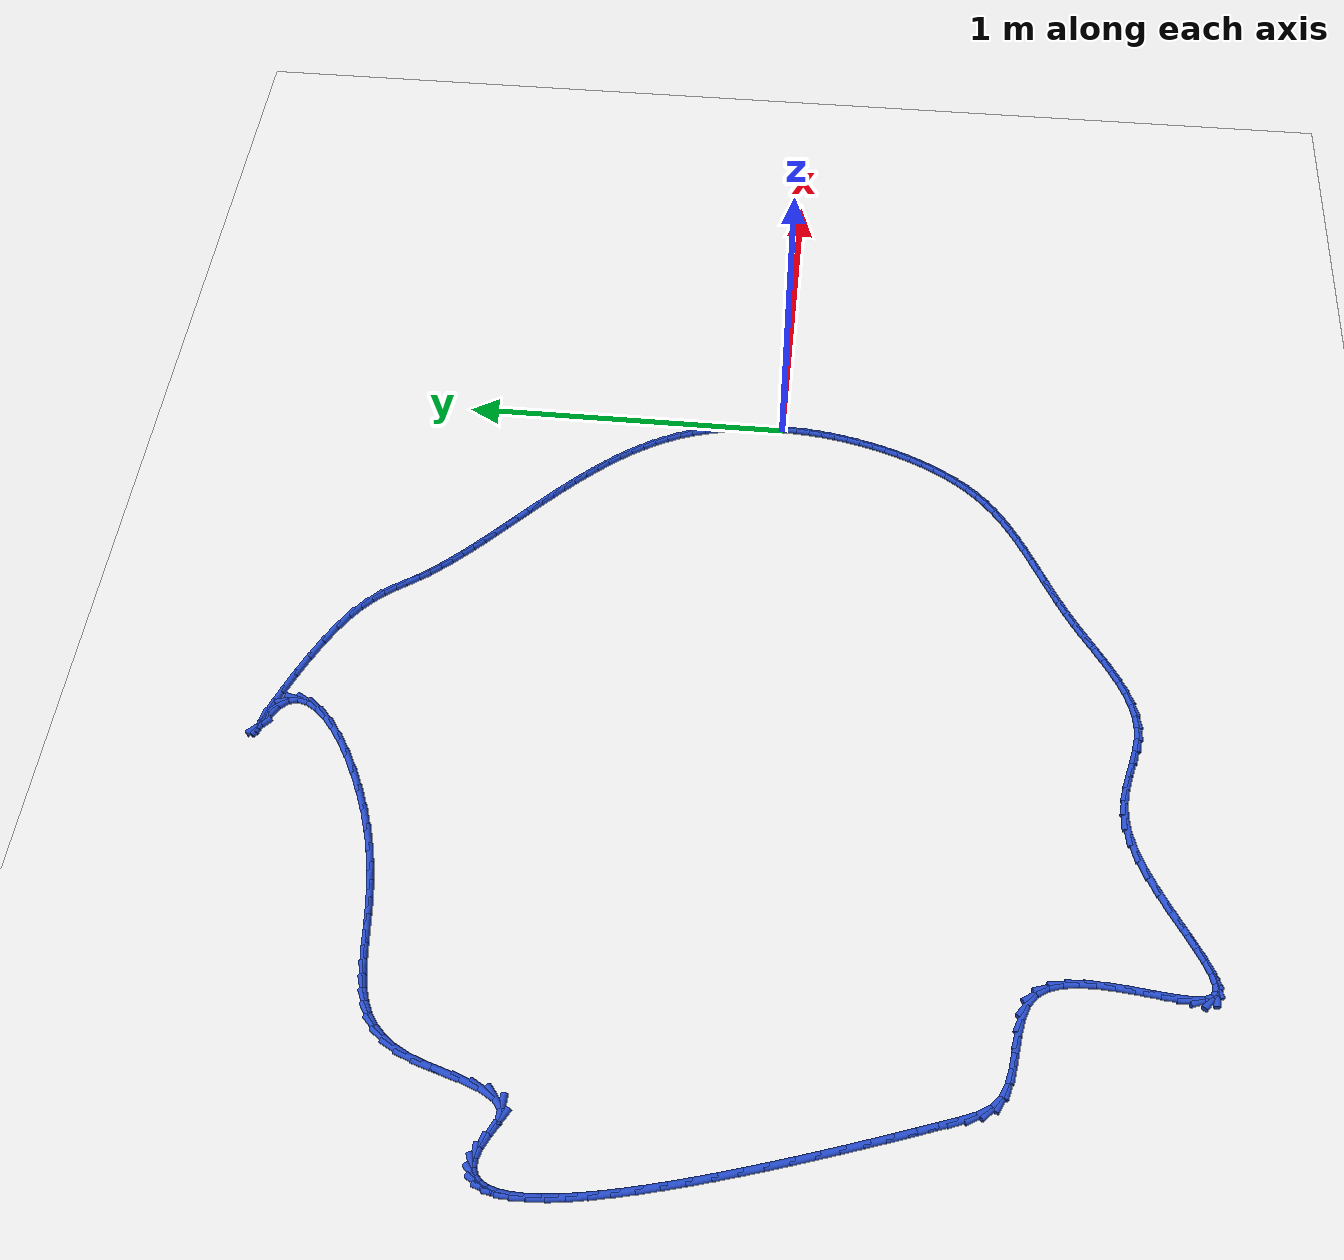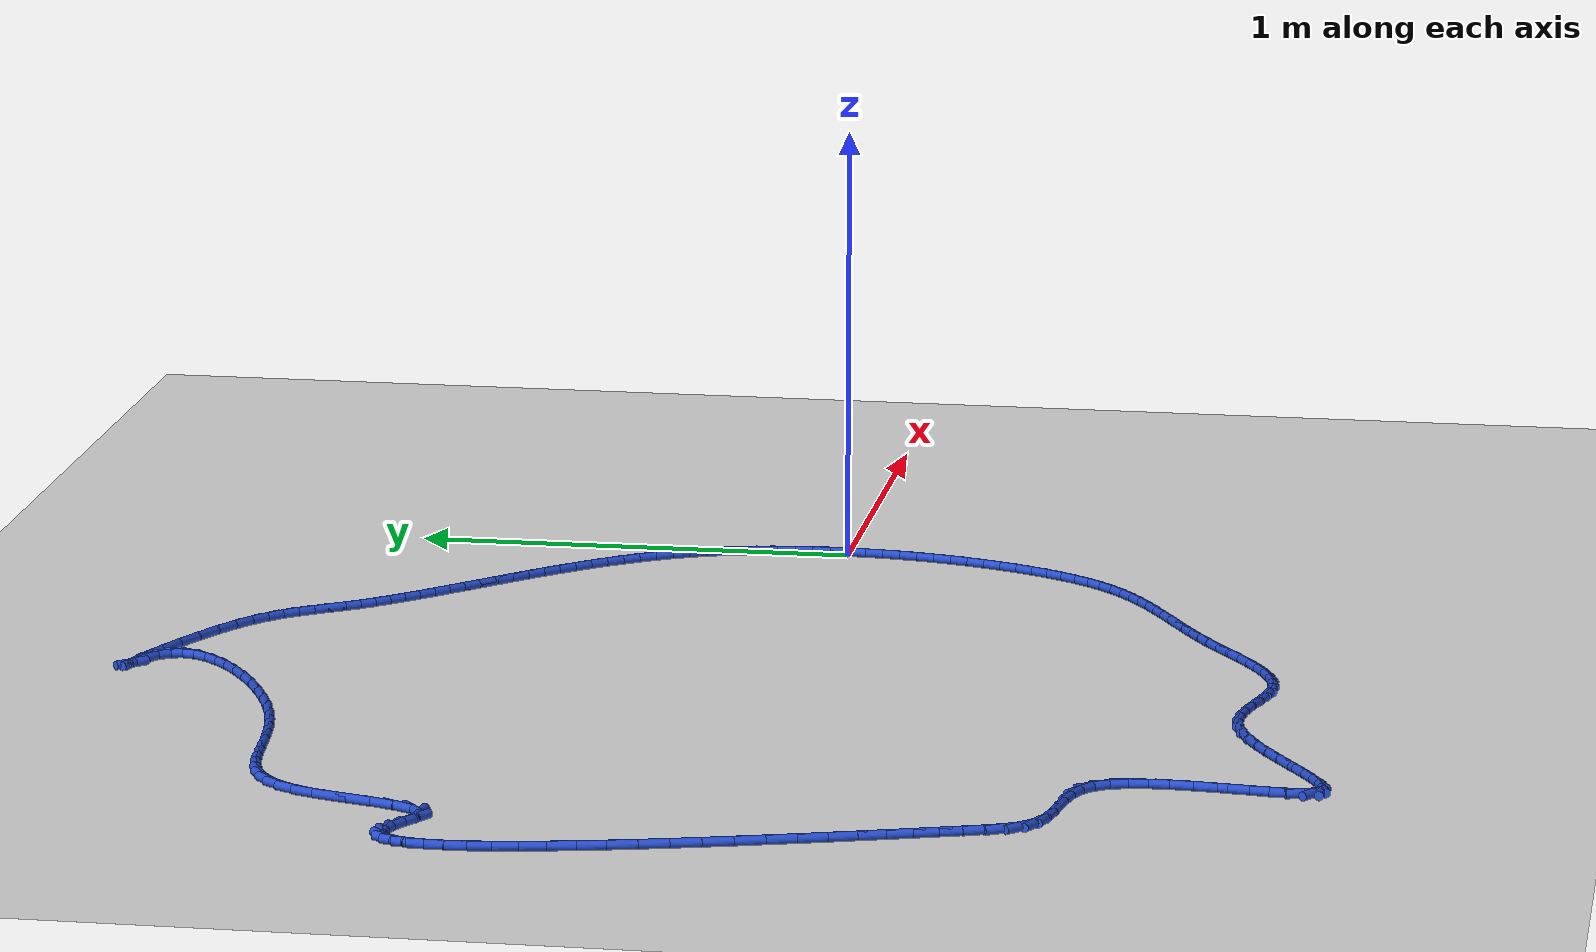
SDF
<sdf version="1.6">
 <world name="default">
  <light name="sun" type="directional">
   <pose>0 0 10 0 -0 0</pose>
   <diffuse>0.8 0.8 0.8 1</diffuse>
   <specular>0.2 0.2 0.2 1</specular>
   <attenuation>
    <range>1000</range>
    <constant>0.9</constant>
    <linear>0.01</linear>
    <quadratic>0.001</quadratic>
   </attenuation>
   <direction>-0.5 0.1 -0.9</direction>
  </light>
  <model name="ground_plane">
   <static>1</static>
   <link name="link">
    <collision name="collision">
     <geometry><plane><normal>0 0 1</normal><size>100 100</size></plane></geometry>
     <surface><friction><ode><mu>100</mu><mu2>50</mu2></ode></friction></surface>
    </collision>
    <visual name="visual">
     <cast_shadows>0</cast_shadows>
     <geometry><plane><normal>0 0 1</normal><size>100 100</size></plane></geometry>
     <material>
      <script><uri>file://media/materials/scripts/gazebo.material</uri><name>Gazebo/WhiteGlow</name></script>
     </material>
    </visual>
   </link>
  </model>
  <gravity>0 0 -9.8</gravity>
  <magnetic_field>6e-06 2.3e-05 -4.2e-05</magnetic_field>
  <atmosphere type="adiabatic"/>
  <physics name="default_physics" default="0" type="ode">
   <max_step_size>0.001</max_step_size>
   <real_time_factor>1</real_time_factor>
   <real_time_update_rate>1000</real_time_update_rate>
  </physics>
  <scene><ambient>0.4 0.4 0.4 1</ambient><background>0.7 0.7 0.7 1</background><shadows>1</shadows></scene>
  <spherical_coordinates>
   <surface_model>EARTH_WGS84</surface_model>
   <latitude_deg>0</latitude_deg>
   <longitude_deg>0</longitude_deg>
   <elevation>0</elevation>
   <heading_deg>0</heading_deg>
  </spherical_coordinates>
  <model name="line">
   <link name="link_0">
    <pose>-1.6479873021779667e-17 -8.326672684688674e-17 0.01 0 1.57 -1.566414731328799</pose>
    <collision name="collision">
     <geometry><cylinder><radius>0.01</radius><length>0.08</length></cylinder></geometry>
    </collision>
    <visual name="visual">
     <material>
      <script><name>Gazebo/Blue</name><uri>file://media/materials/scripts/gazebo.material</uri></script>
     </material>
     <geometry><cylinder><radius>0.01</radius><length>0.08</length></cylinder></geometry>
    </visual>
   </link>
   <link name="link_1">
    <pose>-0.00018184845922349167 0.04150252959159567 0.01 0 1.57 -1.5263534469862161</pose>
    <collision name="collision">
     <geometry><cylinder><radius>0.01</radius><length>0.08</length></cylinder></geometry>
    </collision>
    <visual name="visual">
     <material>
      <script><name>Gazebo/Blue</name><uri>file://media/materials/scripts/gazebo.material</uri></script>
     </material>
     <geometry><cylinder><radius>0.01</radius><length>0.08</length></cylinder></geometry>
    </visual>
   </link>
   <link name="link_2">
    <pose>-0.002030293858694147 0.08306662826030879 0.01 0 1.57 -1.4835779898202277</pose>
    <collision name="collision">
     <geometry><cylinder><radius>0.01</radius><length>0.08</length></cylinder></geometry>
    </collision>
    <visual name="visual">
     <material>
      <script><name>Gazebo/Blue</name><uri>file://media/materials/scripts/gazebo.material</uri></script>
     </material>
     <geometry><cylinder><radius>0.01</radius><length>0.08</length></cylinder></geometry>
    </visual>
   </link>
   <link name="link_3">
    <pose>-0.005656570394167152 0.12453814582838611 0.01 0 1.57 -1.4377990456804615</pose>
    <collision name="collision">
     <geometry><cylinder><radius>0.01</radius><length>0.08</length></cylinder></geometry>
    </collision>
    <visual name="visual">
     <material>
      <script><name>Gazebo/Blue</name><uri>file://media/materials/scripts/gazebo.material</uri></script>
     </material>
     <geometry><cylinder><radius>0.01</radius><length>0.08</length></cylinder></geometry>
    </visual>
   </link>
   <link name="link_4">
    <pose>-0.011171912261397684 0.16576293211807444 0.01 0 1.57 -1.388735852787313</pose>
    <collision name="collision">
     <geometry><cylinder><radius>0.01</radius><length>0.08</length></cylinder></geometry>
    </collision>
    <visual name="visual">
     <material>
      <script><name>Gazebo/Blue</name><uri>file://media/materials/scripts/gazebo.material</uri></script>
     </material>
     <geometry><cylinder><radius>0.01</radius><length>0.08</length></cylinder></geometry>
    </visual>
   </link>
   <link name="link_5">
    <pose>-0.018687553656140922 0.2065868369516207 0.01 0 1.57 -1.336128635197611</pose>
    <collision name="collision">
     <geometry><cylinder><radius>0.01</radius><length>0.08</length></cylinder></geometry>
    </collision>
    <visual name="visual">
     <material>
      <script><name>Gazebo/Blue</name><uri>file://media/materials/scripts/gazebo.material</uri></script>
     </material>
     <geometry><cylinder><radius>0.01</radius><length>0.08</length></cylinder></geometry>
    </visual>
   </link>
   <link name="link_6">
    <pose>-0.02831472877415203 0.2468557101512717 0.01 0 1.57 -1.2797561973764093</pose>
    <collision name="collision">
     <geometry><cylinder><radius>0.01</radius><length>0.08</length></cylinder></geometry>
    </collision>
    <visual name="visual">
     <material>
      <script><name>Gazebo/Blue</name><uri>file://media/materials/scripts/gazebo.material</uri></script>
     </material>
     <geometry><cylinder><radius>0.01</radius><length>0.08</length></cylinder></geometry>
    </visual>
   </link>
   <link name="link_7">
    <pose>-0.04016467181118619 0.28641540153927414 0.01 0 1.57 -1.219459057804905</pose>
    <collision name="collision">
     <geometry><cylinder><radius>0.01</radius><length>0.08</length></cylinder></geometry>
    </collision>
    <visual name="visual">
     <material>
      <script><name>Gazebo/Blue</name><uri>file://media/materials/scripts/gazebo.material</uri></script>
     </material>
     <geometry><cylinder><radius>0.01</radius><length>0.08</length></cylinder></geometry>
    </visual>
   </link>
   <link name="link_8">
    <pose>-0.05434861689962701 0.32511176098188793 0.01 0 1.57 -1.156680159206354</pose>
    <collision name="collision">
     <geometry><cylinder><radius>0.01</radius><length>0.08</length></cylinder></geometry>
    </collision>
    <visual name="visual">
     <material>
      <script><name>Gazebo/Blue</name><uri>file://media/materials/scripts/gazebo.material</uri></script>
     </material>
     <geometry><cylinder><radius>0.01</radius><length>0.08</length></cylinder></geometry>
    </visual>
   </link>
   <link name="link_9">
    <pose>-0.0709256679759595 0.36282684371516394 0.01 0 1.57 -1.0974165975322892</pose>
    <collision name="collision">
     <geometry><cylinder><radius>0.01</radius><length>0.08</length></cylinder></geometry>
    </collision>
    <visual name="visual">
     <material>
      <script><name>Gazebo/Blue</name><uri>file://media/materials/scripts/gazebo.material</uri></script>
     </material>
     <geometry><cylinder><radius>0.01</radius><length>0.08</length></cylinder></geometry>
    </visual>
   </link>
   <link name="link_10">
    <pose>-0.08975304760563364 0.39958291526146383 0.01 0 1.57 -1.0433117421562952</pose>
    <collision name="collision">
     <geometry><cylinder><radius>0.01</radius><length>0.08</length></cylinder></geometry>
    </collision>
    <visual name="visual">
     <material>
      <script><name>Gazebo/Blue</name><uri>file://media/materials/scripts/gazebo.material</uri></script>
     </material>
     <geometry><cylinder><radius>0.01</radius><length>0.08</length></cylinder></geometry>
    </visual>
   </link>
   <link name="link_11">
    <pose>-0.11063911534300795 0.43543617739363144 0.01 0 1.57 -0.9944454056509866</pose>
    <collision name="collision">
     <geometry><cylinder><radius>0.01</radius><length>0.08</length></cylinder></geometry>
    </collision>
    <visual name="visual">
     <material>
      <script><name>Gazebo/Blue</name><uri>file://media/materials/scripts/gazebo.material</uri></script>
     </material>
     <geometry><cylinder><radius>0.01</radius><length>0.08</length></cylinder></geometry>
    </visual>
   </link>
   <link name="link_12">
    <pose>-0.13339223074244103 0.4704428318845107 0.01 0 1.57 -0.9507724273365723</pose>
    <collision name="collision">
     <geometry><cylinder><radius>0.01</radius><length>0.08</length></cylinder></geometry>
    </collision>
    <visual name="visual">
     <material>
      <script><name>Gazebo/Blue</name><uri>file://media/materials/scripts/gazebo.material</uri></script>
     </material>
     <geometry><cylinder><radius>0.01</radius><length>0.08</length></cylinder></geometry>
    </visual>
   </link>
   <link name="link_13">
    <pose>-0.15782075335829152 0.504659080506945 0.01 0 1.57 -0.9121638603867378</pose>
    <collision name="collision">
     <geometry><cylinder><radius>0.01</radius><length>0.08</length></cylinder></geometry>
    </collision>
    <visual name="visual">
     <material>
      <script><name>Gazebo/Blue</name><uri>file://media/materials/scripts/gazebo.material</uri></script>
     </material>
     <geometry><cylinder><radius>0.01</radius><length>0.08</length></cylinder></geometry>
    </visual>
   </link>
   <link name="link_14">
    <pose>-0.18373304274491778 0.5381411250337782 0.01 0 1.57 -0.8784426802892685</pose>
    <collision name="collision">
     <geometry><cylinder><radius>0.01</radius><length>0.08</length></cylinder></geometry>
    </collision>
    <visual name="visual">
     <material>
      <script><name>Gazebo/Blue</name><uri>file://media/materials/scripts/gazebo.material</uri></script>
     </material>
     <geometry><cylinder><radius>0.01</radius><length>0.08</length></cylinder></geometry>
    </visual>
   </link>
   <link name="link_15">
    <pose>-0.21093745845667858 0.5709451672378543 0.01 0 1.57 -0.8494124675856856</pose>
    <collision name="collision">
     <geometry><cylinder><radius>0.01</radius><length>0.08</length></cylinder></geometry>
    </collision>
    <visual name="visual">
     <material>
      <script><name>Gazebo/Blue</name><uri>file://media/materials/scripts/gazebo.material</uri></script>
     </material>
     <geometry><cylinder><radius>0.01</radius><length>0.08</length></cylinder></geometry>
    </visual>
   </link>
   <link name="link_16">
    <pose>-0.23924236004793248 0.6031274088920169 0.01 0 1.57 -0.824879206002455</pose>
    <collision name="collision">
     <geometry><cylinder><radius>0.01</radius><length>0.08</length></cylinder></geometry>
    </collision>
    <visual name="visual">
     <material>
      <script><name>Gazebo/Blue</name><uri>file://media/materials/scripts/gazebo.material</uri></script>
     </material>
     <geometry><cylinder><radius>0.01</radius><length>0.08</length></cylinder></geometry>
    </visual>
   </link>
   <link name="link_17">
    <pose>-0.268456107073038 0.6347440517691096 0.01 0 1.57 -0.8046672164186457</pose>
    <collision name="collision">
     <geometry><cylinder><radius>0.01</radius><length>0.08</length></cylinder></geometry>
    </collision>
    <visual name="visual">
     <material>
      <script><name>Gazebo/Blue</name><uri>file://media/materials/scripts/gazebo.material</uri></script>
     </material>
     <geometry><cylinder><radius>0.01</radius><length>0.08</length></cylinder></geometry>
    </visual>
   </link>
   <link name="link_18">
    <pose>-0.2983870590863537 0.6658512976419765 0.01 0 1.57 -0.7886305568555553</pose>
    <collision name="collision">
     <geometry><cylinder><radius>0.01</radius><length>0.08</length></cylinder></geometry>
    </collision>
    <visual name="visual">
     <material>
      <script><name>Gazebo/Blue</name><uri>file://media/materials/scripts/gazebo.material</uri></script>
     </material>
     <geometry><cylinder><radius>0.01</radius><length>0.08</length></cylinder></geometry>
    </visual>
   </link>
   <link name="link_19">
    <pose>-0.3288435756422382 0.696505348283461 0.01 0 1.57 -0.7766611976439031</pose>
    <collision name="collision">
     <geometry><cylinder><radius>0.01</radius><length>0.08</length></cylinder></geometry>
    </collision>
    <visual name="visual">
     <material>
      <script><name>Gazebo/Blue</name><uri>file://media/materials/scripts/gazebo.material</uri></script>
     </material>
     <geometry><cylinder><radius>0.01</radius><length>0.08</length></cylinder></geometry>
    </visual>
   </link>
   <link name="link_20">
    <pose>-0.35963401629505 0.726762405466407 0.01 0 1.57 -0.7686951042277733</pose>
    <collision name="collision">
     <geometry><cylinder><radius>0.01</radius><length>0.08</length></cylinder></geometry>
    </collision>
    <visual name="visual">
     <material>
      <script><name>Gazebo/Blue</name><uri>file://media/materials/scripts/gazebo.material</uri></script>
     </material>
     <geometry><cylinder><radius>0.01</radius><length>0.08</length></cylinder></geometry>
    </visual>
   </link>
   <link name="link_21">
    <pose>-0.3905667405991477 0.7566786709636583 0.01 0 1.57 -0.7647171326220001</pose>
    <collision name="collision">
     <geometry><cylinder><radius>0.01</radius><length>0.08</length></cylinder></geometry>
    </collision>
    <visual name="visual">
     <material>
      <script><name>Gazebo/Blue</name><uri>file://media/materials/scripts/gazebo.material</uri></script>
     </material>
     <geometry><cylinder><radius>0.01</radius><length>0.08</length></cylinder></geometry>
    </visual>
   </link>
   <link name="link_22">
    <pose>-0.42145010810888994 0.7863103465480586 0.01 0 1.57 -0.7647654142961193</pose>
    <collision name="collision">
     <geometry><cylinder><radius>0.01</radius><length>0.08</length></cylinder></geometry>
    </collision>
    <visual name="visual">
     <material>
      <script><name>Gazebo/Blue</name><uri>file://media/materials/scripts/gazebo.material</uri></script>
     </material>
     <geometry><cylinder><radius>0.01</radius><length>0.08</length></cylinder></geometry>
    </visual>
   </link>
   <link name="link_23">
    <pose>-0.4520924783786352 0.8157136339924517 0.01 0 1.57 -0.7689356907550452</pose>
    <collision name="collision">
     <geometry><cylinder><radius>0.01</radius><length>0.08</length></cylinder></geometry>
    </collision>
    <visual name="visual">
     <material>
      <script><name>Gazebo/Blue</name><uri>file://media/materials/scripts/gazebo.material</uri></script>
     </material>
     <geometry><cylinder><radius>0.01</radius><length>0.08</length></cylinder></geometry>
    </visual>
   </link>
   <link name="link_24">
    <pose>-0.4823022109627422 0.8449447350696813 0.01 0 1.57 -0.7773858409009967</pose>
    <collision name="collision">
     <geometry><cylinder><radius>0.01</radius><length>0.08</length></cylinder></geometry>
    </collision>
    <visual name="visual">
     <material>
      <script><name>Gazebo/Blue</name><uri>file://media/materials/scripts/gazebo.material</uri></script>
     </material>
     <geometry><cylinder><radius>0.01</radius><length>0.08</length></cylinder></geometry>
    </visual>
   </link>
   <link name="link_25">
    <pose>-0.5118876654155692 0.8740598515525911 0.01 0 1.57 -0.7903405949271696</pose>
    <collision name="collision">
     <geometry><cylinder><radius>0.01</radius><length>0.08</length></cylinder></geometry>
    </collision>
    <visual name="visual">
     <material>
      <script><name>Gazebo/Blue</name><uri>file://media/materials/scripts/gazebo.material</uri></script>
     </material>
     <geometry><cylinder><radius>0.01</radius><length>0.08</length></cylinder></geometry>
    </visual>
   </link>
   <link name="link_26">
    <pose>-0.5406572012914752 0.9031151852140251 0.01 0 1.57 -0.8080960969447941</pose>
    <collision name="collision">
     <geometry><cylinder><radius>0.01</radius><length>0.08</length></cylinder></geometry>
    </collision>
    <visual name="visual">
     <material>
      <script><name>Gazebo/Blue</name><uri>file://media/materials/scripts/gazebo.material</uri></script>
     </material>
     <geometry><cylinder><radius>0.01</radius><length>0.08</length></cylinder></geometry>
    </visual>
   </link>
   <link name="link_27">
    <pose>-0.5684191781448183 0.9321669378268269 0.01 0 1.57 -0.8310234933361021</pose>
    <collision name="collision">
     <geometry><cylinder><radius>0.01</radius><length>0.08</length></cylinder></geometry>
    </collision>
    <visual name="visual">
     <material>
      <script><name>Gazebo/Blue</name><uri>file://media/materials/scripts/gazebo.material</uri></script>
     </material>
     <geometry><cylinder><radius>0.01</radius><length>0.08</length></cylinder></geometry>
    </visual>
   </link>
   <link name="link_28">
    <pose>-0.5949819555299574 0.96127131116384 0.01 0 1.57 -0.8595699904722489</pose>
    <collision name="collision">
     <geometry><cylinder><radius>0.01</radius><length>0.08</length></cylinder></geometry>
    </collision>
    <visual name="visual">
     <material>
      <script><name>Gazebo/Blue</name><uri>file://media/materials/scripts/gazebo.material</uri></script>
     </material>
     <geometry><cylinder><radius>0.01</radius><length>0.08</length></cylinder></geometry>
    </visual>
   </link>
   <link name="link_29">
    <pose>-0.6201538930012511 0.9904845069979088 0.01 0 1.57 -0.8942547354429592</pose>
    <collision name="collision">
     <geometry><cylinder><radius>0.01</radius><length>0.08</length></cylinder></geometry>
    </collision>
    <visual name="visual">
     <material>
      <script><name>Gazebo/Blue</name><uri>file://media/materials/scripts/gazebo.material</uri></script>
     </material>
     <geometry><cylinder><radius>0.01</radius><length>0.08</length></cylinder></geometry>
    </visual>
   </link>
   <link name="link_30">
    <pose>-0.6437433501130578 1.019862727101876 0.01 0 1.57 -0.9356553446952278</pose>
    <collision name="collision">
     <geometry><cylinder><radius>0.01</radius><length>0.08</length></cylinder></geometry>
    </collision>
    <visual name="visual">
     <material>
      <script><name>Gazebo/Blue</name><uri>file://media/materials/scripts/gazebo.material</uri></script>
     </material>
     <geometry><cylinder><radius>0.01</radius><length>0.08</length></cylinder></geometry>
    </visual>
   </link>
   <link name="link_31">
    <pose>-0.6655586864197363 1.0494621732485867 0.01 0 1.57 -0.9759534143175839</pose>
    <collision name="collision">
     <geometry><cylinder><radius>0.01</radius><length>0.08</length></cylinder></geometry>
    </collision>
    <visual name="visual">
     <material>
      <script><name>Gazebo/Blue</name><uri>file://media/materials/scripts/gazebo.material</uri></script>
     </material>
     <geometry><cylinder><radius>0.01</radius><length>0.08</length></cylinder></geometry>
    </visual>
   </link>
   <link name="link_32">
    <pose>-0.6857666283754984 1.079329399103206 0.01 0 1.57 -0.9794229629001187</pose>
    <collision name="collision">
     <geometry><cylinder><radius>0.01</radius><length>0.08</length></cylinder></geometry>
    </collision>
    <visual name="visual">
     <material>
      <script><name>Gazebo/Blue</name><uri>file://media/materials/scripts/gazebo.material</uri></script>
     </material>
     <geometry><cylinder><radius>0.01</radius><length>0.08</length></cylinder></geometry>
    </visual>
   </link>
   <link name="link_33">
    <pose>-0.7060082931679487 1.1094712641499915 0.01 0 1.57 -0.9382048390278432</pose>
    <collision name="collision">
     <geometry><cylinder><radius>0.01</radius><length>0.08</length></cylinder></geometry>
    </collision>
    <visual name="visual">
     <material>
      <script><name>Gazebo/Blue</name><uri>file://media/materials/scripts/gazebo.material</uri></script>
     </material>
     <geometry><cylinder><radius>0.01</radius><length>0.08</length></cylinder></geometry>
    </visual>
   </link>
   <link name="link_34">
    <pose>-0.728303916838107 1.139884421072512 0.01 0 1.57 -0.8608238318364018</pose>
    <collision name="collision">
     <geometry><cylinder><radius>0.01</radius><length>0.08</length></cylinder></geometry>
    </collision>
    <visual name="visual">
     <material>
      <script><name>Gazebo/Blue</name><uri>file://media/materials/scripts/gazebo.material</uri></script>
     </material>
     <geometry><cylinder><radius>0.01</radius><length>0.08</length></cylinder></geometry>
    </visual>
   </link>
   <link name="link_35">
    <pose>-0.7546737357314608 1.1705655225461382 0.01 0 1.57 -0.7614545776031008</pose>
    <collision name="collision">
     <geometry><cylinder><radius>0.01</radius><length>0.08</length></cylinder></geometry>
    </collision>
    <visual name="visual">
     <material>
      <script><name>Gazebo/Blue</name><uri>file://media/materials/scripts/gazebo.material</uri></script>
     </material>
     <geometry><cylinder><radius>0.01</radius><length>0.08</length></cylinder></geometry>
    </visual>
   </link>
   <link name="link_36">
    <pose>-0.787137986193498 1.2015112212462418 0.01 0 1.57 -0.6555778886582705</pose>
    <collision name="collision">
     <geometry><cylinder><radius>0.01</radius><length>0.08</length></cylinder></geometry>
    </collision>
    <visual name="visual">
     <material>
      <script><name>Gazebo/Blue</name><uri>file://media/materials/scripts/gazebo.material</uri></script>
     </material>
     <geometry><cylinder><radius>0.01</radius><length>0.08</length></cylinder></geometry>
    </visual>
   </link>
   <link name="link_37">
    <pose>-0.8277169045697061 1.2327181698481937 0.01 0 1.57 -0.5586795351515282</pose>
    <collision name="collision">
     <geometry><cylinder><radius>0.01</radius><length>0.08</length></cylinder></geometry>
    </collision>
    <visual name="visual">
     <material>
      <script><name>Gazebo/Blue</name><uri>file://media/materials/scripts/gazebo.material</uri></script>
     </material>
     <geometry><cylinder><radius>0.01</radius><length>0.08</length></cylinder></geometry>
    </visual>
   </link>
   <link name="link_38">
    <pose>-0.877895201160869 1.2640852031718677 0.01 0 1.57 -0.49127846712354617</pose>
    <collision name="collision">
     <geometry><cylinder><radius>0.01</radius><length>0.08</length></cylinder></geometry>
    </collision>
    <visual name="visual">
     <material>
      <script><name>Gazebo/Blue</name><uri>file://media/materials/scripts/gazebo.material</uri></script>
     </material>
     <geometry><cylinder><radius>0.01</radius><length>0.08</length></cylinder></geometry>
    </visual>
   </link>
   <link name="link_39">
    <pose>-0.9353225960276756 1.2948106662573213 0.01 0 1.57 -0.4456797730149744</pose>
    <collision name="collision">
     <geometry><cylinder><radius>0.01</radius><length>0.08</length></cylinder></geometry>
    </collision>
    <visual name="visual">
     <material>
      <script><name>Gazebo/Blue</name><uri>file://media/materials/scripts/gazebo.material</uri></script>
     </material>
     <geometry><cylinder><radius>0.01</radius><length>0.08</length></cylinder></geometry>
    </visual>
   </link>
   <link name="link_40">
    <pose>-0.9959768888260876 1.3237875153214698 0.01 0 1.57 -0.4114936196845546</pose>
    <collision name="collision">
     <geometry><cylinder><radius>0.01</radius><length>0.08</length></cylinder></geometry>
    </collision>
    <visual name="visual">
     <material>
      <script><name>Gazebo/Blue</name><uri>file://media/materials/scripts/gazebo.material</uri></script>
     </material>
     <geometry><cylinder><radius>0.01</radius><length>0.08</length></cylinder></geometry>
    </visual>
   </link>
   <link name="link_41">
    <pose>-1.0558289479342888 1.349907440531269 0.01 0 1.57 -0.3827982972189128</pose>
    <collision name="collision">
     <geometry><cylinder><radius>0.01</radius><length>0.08</length></cylinder></geometry>
    </collision>
    <visual name="visual">
     <material>
      <script><name>Gazebo/Blue</name><uri>file://media/materials/scripts/gazebo.material</uri></script>
     </material>
     <geometry><cylinder><radius>0.01</radius><length>0.08</length></cylinder></geometry>
    </visual>
   </link>
   <link name="link_42">
    <pose>-1.1108496417304634 1.3720621320536743 0.01 0 1.57 -0.3544156499729854</pose>
    <collision name="collision">
     <geometry><cylinder><radius>0.01</radius><length>0.08</length></cylinder></geometry>
    </collision>
    <visual name="visual">
     <material>
      <script><name>Gazebo/Blue</name><uri>file://media/materials/scripts/gazebo.material</uri></script>
     </material>
     <geometry><cylinder><radius>0.01</radius><length>0.08</length></cylinder></geometry>
    </visual>
   </link>
   <link name="link_43">
    <pose>-1.1570098385927952 1.389143280055641 0.01 0 1.57 -0.3165778140580224</pose>
    <collision name="collision">
     <geometry><cylinder><radius>0.01</radius><length>0.08</length></cylinder></geometry>
    </collision>
    <visual name="visual">
     <material>
      <script><name>Gazebo/Blue</name><uri>file://media/materials/scripts/gazebo.material</uri></script>
     </material>
     <geometry><cylinder><radius>0.01</radius><length>0.08</length></cylinder></geometry>
    </visual>
   </link>
   <link name="link_44">
    <pose>-1.1902804068994681 1.4000425747041239 0.01 0 1.57 -0.21723465099847283</pose>
    <collision name="collision">
     <geometry><cylinder><radius>0.01</radius><length>0.08</length></cylinder></geometry>
    </collision>
    <visual name="visual">
     <material>
      <script><name>Gazebo/Blue</name><uri>file://media/materials/scripts/gazebo.material</uri></script>
     </material>
     <geometry><cylinder><radius>0.01</radius><length>0.08</length></cylinder></geometry>
    </visual>
   </link>
   <link name="link_45">
    <pose>-1.2066322150286655 1.4036517061660783 0.01 0 1.57 -0.8059865305686704</pose>
    <collision name="collision">
     <geometry><cylinder><radius>0.01</radius><length>0.08</length></cylinder></geometry>
    </collision>
    <visual name="visual">
     <material>
      <script><name>Gazebo/Blue</name><uri>file://media/materials/scripts/gazebo.material</uri></script>
     </material>
     <geometry><cylinder><radius>0.01</radius><length>0.08</length></cylinder></geometry>
    </visual>
   </link>
   <link name="link_46">
    <pose>-1.2020361313585717 1.39886236460846 0.01 0 1.57 -0.45744773224326546</pose>
    <collision name="collision">
     <geometry><cylinder><radius>0.01</radius><length>0.08</length></cylinder></geometry>
    </collision>
    <visual name="visual">
     <material>
      <script><name>Gazebo/Blue</name><uri>file://media/materials/scripts/gazebo.material</uri></script>
     </material>
     <geometry><cylinder><radius>0.01</radius><length>0.08</length></cylinder></geometry>
    </visual>
   </link>
   <link name="link_47">
    <pose>-1.1732487988447886 1.384691109133771 0.01 0 1.57 -0.5398095295319212</pose>
    <collision name="collision">
     <geometry><cylinder><radius>0.01</radius><length>0.08</length></cylinder></geometry>
    </collision>
    <visual name="visual">
     <material>
      <script><name>Gazebo/Blue</name><uri>file://media/materials/scripts/gazebo.material</uri></script>
     </material>
     <geometry><cylinder><radius>0.01</radius><length>0.08</length></cylinder></geometry>
    </visual>
   </link>
   <link name="link_48">
    <pose>-1.1378557610351032 1.3634846363657314 0.01 0 1.57 -0.8729499971255757</pose>
    <collision name="collision">
     <geometry><cylinder><radius>0.01</radius><length>0.08</length></cylinder></geometry>
    </collision>
    <visual name="visual">
     <material>
      <script><name>Gazebo/Blue</name><uri>file://media/materials/scripts/gazebo.material</uri></script>
     </material>
     <geometry><cylinder><radius>0.01</radius><length>0.08</length></cylinder></geometry>
    </visual>
   </link>
   <link name="link_49">
    <pose>-1.11713002952144 1.3387703517172391 0.01 0 1.57 -1.345762738271965</pose>
    <collision name="collision">
     <geometry><cylinder><radius>0.01</radius><length>0.08</length></cylinder></geometry>
    </collision>
    <visual name="visual">
     <material>
      <script><name>Gazebo/Blue</name><uri>file://media/materials/scripts/gazebo.material</uri></script>
     </material>
     <geometry><cylinder><radius>0.01</radius><length>0.08</length></cylinder></geometry>
    </visual>
   </link>
   <link name="link_50">
    <pose>-1.1108504371868106 1.3113378558702198 0.01 0 1.57 1.347301790602479</pose>
    <collision name="collision">
     <geometry><cylinder><radius>0.01</radius><length>0.08</length></cylinder></geometry>
    </collision>
    <visual name="visual">
     <material>
      <script><name>Gazebo/Blue</name><uri>file://media/materials/scripts/gazebo.material</uri></script>
     </material>
     <geometry><cylinder><radius>0.01</radius><length>0.08</length></cylinder></geometry>
    </visual>
   </link>
   <link name="link_51">
    <pose>-1.1175602126354645 1.2818172938286727 0.01 0 1.57 1.0385991122041263</pose>
    <collision name="collision">
     <geometry><cylinder><radius>0.01</radius><length>0.08</length></cylinder></geometry>
    </collision>
    <visual name="visual">
     <material>
      <script><name>Gazebo/Blue</name><uri>file://media/materials/scripts/gazebo.material</uri></script>
     </material>
     <geometry><cylinder><radius>0.01</radius><length>0.08</length></cylinder></geometry>
    </visual>
   </link>
   <link name="link_52">
    <pose>-1.1358025844716493 1.2508388105965973 0.01 0 1.57 0.8433472496219077</pose>
    <collision name="collision">
     <geometry><cylinder><radius>0.01</radius><length>0.08</length></cylinder></geometry>
    </collision>
    <visual name="visual">
     <material>
      <script><name>Gazebo/Blue</name><uri>file://media/materials/scripts/gazebo.material</uri></script>
     </material>
     <geometry><cylinder><radius>0.01</radius><length>0.08</length></cylinder></geometry>
    </visual>
   </link>
   <link name="link_53">
    <pose>-1.1641207812996137 1.2190325511779927 0.01 0 1.57 0.7139609230397266</pose>
    <collision name="collision">
     <geometry><cylinder><radius>0.01</radius><length>0.08</length></cylinder></geometry>
    </collision>
    <visual name="visual">
     <material>
      <script><name>Gazebo/Blue</name><uri>file://media/materials/scripts/gazebo.material</uri></script>
     </material>
     <geometry><cylinder><radius>0.01</radius><length>0.08</length></cylinder></geometry>
    </visual>
   </link>
   <link name="link_54">
    <pose>-1.2010580317236055 1.1870286605768579 0.01 0 1.57 0.6213254055115245</pose>
    <collision name="collision">
     <geometry><cylinder><radius>0.01</radius><length>0.08</length></cylinder></geometry>
    </collision>
    <visual name="visual">
     <material>
      <script><name>Gazebo/Blue</name><uri>file://media/materials/scripts/gazebo.material</uri></script>
     </material>
     <geometry><cylinder><radius>0.01</radius><length>0.08</length></cylinder></geometry>
    </visual>
   </link>
   <link name="link_55">
    <pose>-1.2451575643478734 1.155457283797192 0.01 0 1.57 0.5496056958077886</pose>
    <collision name="collision">
     <geometry><cylinder><radius>0.01</radius><length>0.08</length></cylinder></geometry>
    </collision>
    <visual name="visual">
     <material>
      <script><name>Gazebo/Blue</name><uri>file://media/materials/scripts/gazebo.material</uri></script>
     </material>
     <geometry><cylinder><radius>0.01</radius><length>0.08</length></cylinder></geometry>
    </visual>
   </link>
   <link name="link_56">
    <pose>-1.2949626077766645 1.1249485658429943 0.01 0 1.57 0.4897733787237614</pose>
    <collision name="collision">
     <geometry><cylinder><radius>0.01</radius><length>0.08</length></cylinder></geometry>
    </collision>
    <visual name="visual">
     <material>
      <script><name>Gazebo/Blue</name><uri>file://media/materials/scripts/gazebo.material</uri></script>
     </material>
     <geometry><cylinder><radius>0.01</radius><length>0.08</length></cylinder></geometry>
    </visual>
   </link>
   <link name="link_57">
    <pose>-1.3490163906142287 1.0961326517182635 0.01 0 1.57 0.43612069820958027</pose>
    <collision name="collision">
     <geometry><cylinder><radius>0.01</radius><length>0.08</length></cylinder></geometry>
    </collision>
    <visual name="visual">
     <material>
      <script><name>Gazebo/Blue</name><uri>file://media/materials/scripts/gazebo.material</uri></script>
     </material>
     <geometry><cylinder><radius>0.01</radius><length>0.08</length></cylinder></geometry>
    </visual>
   </link>
   <link name="link_58">
    <pose>-1.4058621414648134 1.0696396864269995 0.01 0 1.57 0.384463527308074</pose>
    <collision name="collision">
     <geometry><cylinder><radius>0.01</radius><length>0.08</length></cylinder></geometry>
    </collision>
    <visual name="visual">
     <material>
      <script><name>Gazebo/Blue</name><uri>file://media/materials/scripts/gazebo.material</uri></script>
     </material>
     <geometry><cylinder><radius>0.01</radius><length>0.08</length></cylinder></geometry>
    </visual>
   </link>
   <link name="link_59">
    <pose>-1.4640430889326659 1.046099814973201 0.01 0 1.57 0.3310764100350629</pose>
    <collision name="collision">
     <geometry><cylinder><radius>0.01</radius><length>0.08</length></cylinder></geometry>
    </collision>
    <visual name="visual">
     <material>
      <script><name>Gazebo/Blue</name><uri>file://media/materials/scripts/gazebo.material</uri></script>
     </material>
     <geometry><cylinder><radius>0.01</radius><length>0.08</length></cylinder></geometry>
    </visual>
   </link>
   <link name="link_60">
    <pose>-1.5221024616220364 1.0261431823608673 0.01 0 1.57 0.27234269560298263</pose>
    <collision name="collision">
     <geometry><cylinder><radius>0.01</radius><length>0.08</length></cylinder></geometry>
    </collision>
    <visual name="visual">
     <material>
      <script><name>Gazebo/Blue</name><uri>file://media/materials/scripts/gazebo.material</uri></script>
     </material>
     <geometry><cylinder><radius>0.01</radius><length>0.08</length></cylinder></geometry>
    </visual>
   </link>
   <link name="link_61">
    <pose>-1.5786220744940083 1.0103582768501222 0.01 0 1.57 0.21402211408506638</pose>
    <collision name="collision">
     <geometry><cylinder><radius>0.01</radius><length>0.08</length></cylinder></geometry>
    </collision>
    <visual name="visual">
     <material>
      <script><name>Gazebo/Blue</name><uri>file://media/materials/scripts/gazebo.material</uri></script>
     </material>
     <geometry><cylinder><radius>0.01</radius><length>0.08</length></cylinder></geometry>
    </visual>
   </link>
   <link name="link_62">
    <pose>-1.6328993216077003 0.9985610676644956 0.01 0 1.57 0.16542133441956647</pose>
    <collision name="collision">
     <geometry><cylinder><radius>0.01</radius><length>0.08</length></cylinder></geometry>
    </collision>
    <visual name="visual">
     <material>
      <script><name>Gazebo/Blue</name><uri>file://media/materials/scripts/gazebo.material</uri></script>
     </material>
     <geometry><cylinder><radius>0.01</radius><length>0.08</length></cylinder></geometry>
    </visual>
   </link>
   <link name="link_63">
    <pose>-1.684862985805638 0.9898858944829764 0.01 0 1.57 0.1291583888164905</pose>
    <collision name="collision">
     <geometry><cylinder><radius>0.01</radius><length>0.08</length></cylinder></geometry>
    </collision>
    <visual name="visual">
     <material>
      <script><name>Gazebo/Blue</name><uri>file://media/materials/scripts/gazebo.material</uri></script>
     </material>
     <geometry><cylinder><radius>0.01</radius><length>0.08</length></cylinder></geometry>
    </visual>
   </link>
   <link name="link_64">
    <pose>-1.7344635154815178 0.983443707465824 0.01 0 1.57 0.1076241426292096</pose>
    <collision name="collision">
     <geometry><cylinder><radius>0.01</radius><length>0.08</length></cylinder></geometry>
    </collision>
    <visual name="visual">
     <material>
      <script><name>Gazebo/Blue</name><uri>file://media/materials/scripts/gazebo.material</uri></script>
     </material>
     <geometry><cylinder><radius>0.01</radius><length>0.08</length></cylinder></geometry>
    </visual>
   </link>
   <link name="link_65">
    <pose>-1.781651359029034 0.9783454567732975 0.01 0 1.57 0.1034483168269459</pose>
    <collision name="collision">
     <geometry><cylinder><radius>0.01</radius><length>0.08</length></cylinder></geometry>
    </collision>
    <visual name="visual">
     <material>
      <script><name>Gazebo/Blue</name><uri>file://media/materials/scripts/gazebo.material</uri></script>
     </material>
     <geometry><cylinder><radius>0.01</radius><length>0.08</length></cylinder></geometry>
    </visual>
   </link>
   <link name="link_66">
    <pose>-1.8263769648418817 0.9737020925656564 0.01 0 1.57 0.11970610305795841</pose>
    <collision name="collision">
     <geometry><cylinder><radius>0.01</radius><length>0.08</length></cylinder></geometry>
    </collision>
    <visual name="visual">
     <material>
      <script><name>Gazebo/Blue</name><uri>file://media/materials/scripts/gazebo.material</uri></script>
     </material>
     <geometry><cylinder><radius>0.01</radius><length>0.08</length></cylinder></geometry>
    </visual>
   </link>
   <link name="link_67">
    <pose>-1.8685907813137566 0.9686245650031597 0.01 0 1.57 0.16004044790419905</pose>
    <collision name="collision">
     <geometry><cylinder><radius>0.01</radius><length>0.08</length></cylinder></geometry>
    </collision>
    <visual name="visual">
     <material>
      <script><name>Gazebo/Blue</name><uri>file://media/materials/scripts/gazebo.material</uri></script>
     </material>
     <geometry><cylinder><radius>0.01</radius><length>0.08</length></cylinder></geometry>
    </visual>
   </link>
   <link name="link_68">
    <pose>-1.9082432568383525 0.9622238242460667 0.01 0 1.57 0.22846288739029555</pose>
    <collision name="collision">
     <geometry><cylinder><radius>0.01</radius><length>0.08</length></cylinder></geometry>
    </collision>
    <visual name="visual">
     <material>
      <script><name>Gazebo/Blue</name><uri>file://media/materials/scripts/gazebo.material</uri></script>
     </material>
     <geometry><cylinder><radius>0.01</radius><length>0.08</length></cylinder></geometry>
    </visual>
   </link>
   <link name="link_69">
    <pose>-1.9452848398093665 0.953610820454637 0.01 0 1.57 0.3283831075032461</pose>
    <collision name="collision">
     <geometry><cylinder><radius>0.01</radius><length>0.08</length></cylinder></geometry>
    </collision>
    <visual name="visual">
     <material>
      <script><name>Gazebo/Blue</name><uri>file://media/materials/scripts/gazebo.material</uri></script>
     </material>
     <geometry><cylinder><radius>0.01</radius><length>0.08</length></cylinder></geometry>
    </visual>
   </link>
   <link name="link_70">
    <pose>-1.9796659786204909 0.9418965037891289 0.01 0 1.57 0.46033586480324795</pose>
    <collision name="collision">
     <geometry><cylinder><radius>0.01</radius><length>0.08</length></cylinder></geometry>
    </collision>
    <visual name="visual">
     <material>
      <script><name>Gazebo/Blue</name><uri>file://media/materials/scripts/gazebo.material</uri></script>
     </material>
     <geometry><cylinder><radius>0.01</radius><length>0.08</length></cylinder></geometry>
    </visual>
   </link>
   <link name="link_71">
    <pose>-2.0113371216654237 0.9261918244098029 0.01 0 1.57 0.6187122047595729</pose>
    <collision name="collision">
     <geometry><cylinder><radius>0.01</radius><length>0.08</length></cylinder></geometry>
    </collision>
    <visual name="visual">
     <material>
      <script><name>Gazebo/Blue</name><uri>file://media/materials/scripts/gazebo.material</uri></script>
     </material>
     <geometry><cylinder><radius>0.01</radius><length>0.08</length></cylinder></geometry>
    </visual>
   </link>
   <link name="link_72">
    <pose>-2.0402487173378585 0.9056077324769174 0.01 0 1.57 0.7901652112512412</pose>
    <collision name="collision">
     <geometry><cylinder><radius>0.01</radius><length>0.08</length></cylinder></geometry>
    </collision>
    <visual name="visual">
     <material>
      <script><name>Gazebo/Blue</name><uri>file://media/materials/scripts/gazebo.material</uri></script>
     </material>
     <geometry><cylinder><radius>0.01</radius><length>0.08</length></cylinder></geometry>
    </visual>
   </link>
   <link name="link_73">
    <pose>-2.066351214031491 0.8792551781507323 0.01 0 1.57 0.957294448054518</pose>
    <collision name="collision">
     <geometry><cylinder><radius>0.01</radius><length>0.08</length></cylinder></geometry>
    </collision>
    <visual name="visual">
     <material>
      <script><name>Gazebo/Blue</name><uri>file://media/materials/scripts/gazebo.material</uri></script>
     </material>
     <geometry><cylinder><radius>0.01</radius><length>0.08</length></cylinder></geometry>
    </visual>
   </link>
   <link name="link_74">
    <pose>-2.0895950601400153 0.846245111591506 0.01 0 1.57 1.1060185019705449</pose>
    <collision name="collision">
     <geometry><cylinder><radius>0.01</radius><length>0.08</length></cylinder></geometry>
    </collision>
    <visual name="visual">
     <material>
      <script><name>Gazebo/Blue</name><uri>file://media/materials/scripts/gazebo.material</uri></script>
     </material>
     <geometry><cylinder><radius>0.01</radius><length>0.08</length></cylinder></geometry>
    </visual>
   </link>
   <link name="link_75">
    <pose>-2.109930704057128 0.8056884829594981 0.01 0 1.57 1.2240671550056765</pose>
    <collision name="collision">
     <geometry><cylinder><radius>0.01</radius><length>0.08</length></cylinder></geometry>
    </collision>
    <visual name="visual">
     <material>
      <script><name>Gazebo/Blue</name><uri>file://media/materials/scripts/gazebo.material</uri></script>
     </material>
     <geometry><cylinder><radius>0.01</radius><length>0.08</length></cylinder></geometry>
    </visual>
   </link>
   <link name="link_76">
    <pose>-2.1274466192430586 0.757211752561746 0.01 0 1.57 1.2807468877456092</pose>
    <collision name="collision">
     <geometry><cylinder><radius>0.01</radius><length>0.08</length></cylinder></geometry>
    </collision>
    <visual name="visual">
     <material>
      <script><name>Gazebo/Blue</name><uri>file://media/materials/scripts/gazebo.material</uri></script>
     </material>
     <geometry><cylinder><radius>0.01</radius><length>0.08</length></cylinder></geometry>
    </visual>
   </link>
   <link name="link_77">
    <pose>-2.1432523965544554 0.7042551544792494 0.01 0 1.57 1.27973114985631</pose>
    <collision name="collision">
     <geometry><cylinder><radius>0.01</radius><length>0.08</length></cylinder></geometry>
    </collision>
    <visual name="visual">
     <material>
      <script><name>Gazebo/Blue</name><uri>file://media/materials/scripts/gazebo.material</uri></script>
     </material>
     <geometry><cylinder><radius>0.01</radius><length>0.08</length></cylinder></geometry>
    </visual>
   </link>
   <link name="link_78">
    <pose>-2.158915696429509 0.6519697679542762 0.01 0 1.57 1.2182674494885746</pose>
    <collision name="collision">
     <geometry><cylinder><radius>0.01</radius><length>0.08</length></cylinder></geometry>
    </collision>
    <visual name="visual">
     <material>
      <script><name>Gazebo/Blue</name><uri>file://media/materials/scripts/gazebo.material</uri></script>
     </material>
     <geometry><cylinder><radius>0.01</radius><length>0.08</length></cylinder></geometry>
    </visual>
   </link>
   <link name="link_79">
    <pose>-2.176006348635419 0.6055147744611202 0.01 0 1.57 1.055444475067602</pose>
    <collision name="collision">
     <geometry><cylinder><radius>0.01</radius><length>0.08</length></cylinder></geometry>
    </collision>
    <visual name="visual">
     <material>
      <script><name>Gazebo/Blue</name><uri>file://media/materials/scripts/gazebo.material</uri></script>
     </material>
     <geometry><cylinder><radius>0.01</radius><length>0.08</length></cylinder></geometry>
    </visual>
   </link>
   <link name="link_80">
    <pose>-2.196094182939382 0.570049355474075 0.01 0 1.57 0.6645884004642433</pose>
    <collision name="collision">
     <geometry><cylinder><radius>0.01</radius><length>0.08</length></cylinder></geometry>
    </collision>
    <visual name="visual">
     <material>
      <script><name>Gazebo/Blue</name><uri>file://media/materials/scripts/gazebo.material</uri></script>
     </material>
     <geometry><cylinder><radius>0.01</radius><length>0.08</length></cylinder></geometry>
    </visual>
   </link>
   <link name="link_81">
    <pose>-2.2207490291085956 0.5507326924674331 0.01 0 1.57 -0.06457929460538185</pose>
    <collision name="collision">
     <geometry><cylinder><radius>0.01</radius><length>0.08</length></cylinder></geometry>
    </collision>
    <visual name="visual">
     <material>
      <script><name>Gazebo/Blue</name><uri>file://media/materials/scripts/gazebo.material</uri></script>
     </material>
     <geometry><cylinder><radius>0.01</radius><length>0.08</length></cylinder></geometry>
    </visual>
   </link>
   <link name="link_82">
    <pose>-2.251540716907874 0.5527239669087626 0.01 0 1.57 -0.5212176723333364</pose>
    <collision name="collision">
     <geometry><cylinder><radius>0.01</radius><length>0.08</length></cylinder></geometry>
    </collision>
    <visual name="visual">
     <material>
      <script><name>Gazebo/Blue</name><uri>file://media/materials/scripts/gazebo.material</uri></script>
     </material>
     <geometry><cylinder><radius>0.01</radius><length>0.08</length></cylinder></geometry>
    </visual>
   </link>
   <link name="link_83">
    <pose>-2.2872107349214366 0.5732049713370797 0.01 0 1.57 -0.45755475171365434</pose>
    <collision name="collision">
     <geometry><cylinder><radius>0.01</radius><length>0.08</length></cylinder></geometry>
    </collision>
    <visual name="visual">
     <material>
      <script><name>Gazebo/Blue</name><uri>file://media/materials/scripts/gazebo.material</uri></script>
     </material>
     <geometry><cylinder><radius>0.01</radius><length>0.08</length></cylinder></geometry>
    </visual>
   </link>
   <link name="link_84">
    <pose>-2.3193869982682496 0.5890487875511012 0.01 0 1.57 -0.2726657144193193</pose>
    <collision name="collision">
     <geometry><cylinder><radius>0.01</radius><length>0.08</length></cylinder></geometry>
    </collision>
    <visual name="visual">
     <material>
      <script><name>Gazebo/Blue</name><uri>file://media/materials/scripts/gazebo.material</uri></script>
     </material>
     <geometry><cylinder><radius>0.01</radius><length>0.08</length></cylinder></geometry>
    </visual>
   </link>
   <link name="link_85">
    <pose>-2.346854416713557 0.5967295060703051 0.01 0 1.57 0.0012909783658579485</pose>
    <collision name="collision">
     <geometry><cylinder><radius>0.01</radius><length>0.08</length></cylinder></geometry>
    </collision>
    <visual name="visual">
     <material>
      <script><name>Gazebo/Blue</name><uri>file://media/materials/scripts/gazebo.material</uri></script>
     </material>
     <geometry><cylinder><radius>0.01</radius><length>0.08</length></cylinder></geometry>
    </visual>
   </link>
   <link name="link_86">
    <pose>-2.369838490430835 0.5966998341118928 0.01 0 1.57 0.3711200791959185</pose>
    <collision name="collision">
     <geometry><cylinder><radius>0.01</radius><length>0.08</length></cylinder></geometry>
    </collision>
    <visual name="visual">
     <material>
      <script><name>Gazebo/Blue</name><uri>file://media/materials/scripts/gazebo.material</uri></script>
     </material>
     <geometry><cylinder><radius>0.01</radius><length>0.08</length></cylinder></geometry>
    </visual>
   </link>
   <link name="link_87">
    <pose>-2.3885647195935666 0.5894124788930666 0.01 0 1.57 0.7645039278968464</pose>
    <collision name="collision">
     <geometry><cylinder><radius>0.01</radius><length>0.08</length></cylinder></geometry>
    </collision>
    <visual name="visual">
     <material>
      <script><name>Gazebo/Blue</name><uri>file://media/materials/scripts/gazebo.material</uri></script>
     </material>
     <geometry><cylinder><radius>0.01</radius><length>0.08</length></cylinder></geometry>
    </visual>
   </link>
   <link name="link_88">
    <pose>-2.40325860437523 0.5753201476310278 0.01 0 1.57 1.0814769237981379</pose>
    <collision name="collision">
     <geometry><cylinder><radius>0.01</radius><length>0.08</length></cylinder></geometry>
    </collision>
    <visual name="visual">
     <material>
      <script><name>Gazebo/Blue</name><uri>file://media/materials/scripts/gazebo.material</uri></script>
     </material>
     <geometry><cylinder><radius>0.01</radius><length>0.08</length></cylinder></geometry>
    </visual>
   </link>
   <link name="link_89">
    <pose>-2.4141456449493055 0.5548755475429784 0.01 0 1.57 1.3002768521249777</pose>
    <collision name="collision">
     <geometry><cylinder><radius>0.01</radius><length>0.08</length></cylinder></geometry>
    </collision>
    <visual name="visual">
     <material>
      <script><name>Gazebo/Blue</name><uri>file://media/materials/scripts/gazebo.material</uri></script>
     </material>
     <geometry><cylinder><radius>0.01</radius><length>0.08</length></cylinder></geometry>
    </visual>
   </link>
   <link name="link_90">
    <pose>-2.4214513414892718 0.5285313858461207 0.01 0 1.57 1.4471854708589897</pose>
    <collision name="collision">
     <geometry><cylinder><radius>0.01</radius><length>0.08</length></cylinder></geometry>
    </collision>
    <visual name="visual">
     <material>
      <script><name>Gazebo/Blue</name><uri>file://media/materials/scripts/gazebo.material</uri></script>
     </material>
     <geometry><cylinder><radius>0.01</radius><length>0.08</length></cylinder></geometry>
    </visual>
   </link>
   <link name="link_91">
    <pose>-2.42540119416861 0.49674036975765573 0.01 0 1.57 1.5485217633511086</pose>
    <collision name="collision">
     <geometry><cylinder><radius>0.01</radius><length>0.08</length></cylinder></geometry>
    </collision>
    <visual name="visual">
     <material>
      <script><name>Gazebo/Blue</name><uri>file://media/materials/scripts/gazebo.material</uri></script>
     </material>
     <geometry><cylinder><radius>0.01</radius><length>0.08</length></cylinder></geometry>
    </visual>
   </link>
   <link name="link_92">
    <pose>-2.4262207031607983 0.4599552064947855 0.01 0 1.57 -1.5203792306119441</pose>
    <collision name="collision">
     <geometry><cylinder><radius>0.01</radius><length>0.08</length></cylinder></geometry>
    </collision>
    <visual name="visual">
     <material>
      <script><name>Gazebo/Blue</name><uri>file://media/materials/scripts/gazebo.material</uri></script>
     </material>
     <geometry><cylinder><radius>0.01</radius><length>0.08</length></cylinder></geometry>
    </visual>
   </link>
   <link name="link_93">
    <pose>-2.4241353686393174 0.41862860327471263 0.01 0 1.57 -1.4662653135142485</pose>
    <collision name="collision">
     <geometry><cylinder><radius>0.01</radius><length>0.08</length></cylinder></geometry>
    </collision>
    <visual name="visual">
     <material>
      <script><name>Gazebo/Blue</name><uri>file://media/materials/scripts/gazebo.material</uri></script>
     </material>
     <geometry><cylinder><radius>0.01</radius><length>0.08</length></cylinder></geometry>
    </visual>
   </link>
   <link name="link_94">
    <pose>-2.419370690777646 0.3732132673146377 0.01 0 1.57 -1.4246825879222087</pose>
    <collision name="collision">
     <geometry><cylinder><radius>0.01</radius><length>0.08</length></cylinder></geometry>
    </collision>
    <visual name="visual">
     <material>
      <script><name>Gazebo/Blue</name><uri>file://media/materials/scripts/gazebo.material</uri></script>
     </material>
     <geometry><cylinder><radius>0.01</radius><length>0.08</length></cylinder></geometry>
    </visual>
   </link>
   <link name="link_95">
    <pose>-2.412152169749265 0.324161905831763 0.01 0 1.57 -1.3918760676383977</pose>
    <collision name="collision">
     <geometry><cylinder><radius>0.01</radius><length>0.08</length></cylinder></geometry>
    </collision>
    <visual name="visual">
     <material>
      <script><name>Gazebo/Blue</name><uri>file://media/materials/scripts/gazebo.material</uri></script>
     </material>
     <geometry><cylinder><radius>0.01</radius><length>0.08</length></cylinder></geometry>
    </visual>
   </link>
   <link name="link_96">
    <pose>-2.402705305727653 0.27192722604329045 0.01 0 1.57 -1.3654252690597473</pose>
    <collision name="collision">
     <geometry><cylinder><radius>0.01</radius><length>0.08</length></cylinder></geometry>
    </collision>
    <visual name="visual">
     <material>
      <script><name>Gazebo/Blue</name><uri>file://media/materials/scripts/gazebo.material</uri></script>
     </material>
     <geometry><cylinder><radius>0.01</radius><length>0.08</length></cylinder></geometry>
    </visual>
   </link>
   <link name="link_97">
    <pose>-2.391255598886291 0.21696193516642182 0.01 0 1.57 -1.3437141832600041</pose>
    <collision name="collision">
     <geometry><cylinder><radius>0.01</radius><length>0.08</length></cylinder></geometry>
    </collision>
    <visual name="visual">
     <material>
      <script><name>Gazebo/Blue</name><uri>file://media/materials/scripts/gazebo.material</uri></script>
     </material>
     <geometry><cylinder><radius>0.01</radius><length>0.08</length></cylinder></geometry>
    </visual>
   </link>
   <link name="link_98">
    <pose>-2.378028549398657 0.15971874041836 0.01 0 1.57 -1.3256297490005275</pose>
    <collision name="collision">
     <geometry><cylinder><radius>0.01</radius><length>0.08</length></cylinder></geometry>
    </collision>
    <visual name="visual">
     <material>
      <script><name>Gazebo/Blue</name><uri>file://media/materials/scripts/gazebo.material</uri></script>
     </material>
     <geometry><cylinder><radius>0.01</radius><length>0.08</length></cylinder></geometry>
    </visual>
   </link>
   <link name="link_99">
    <pose>-2.3632496574382316 0.10065034901630457 0.01 0 1.57 -1.3103844633180357</pose>
    <collision name="collision">
     <geometry><cylinder><radius>0.01</radius><length>0.08</length></cylinder></geometry>
    </collision>
    <visual name="visual">
     <material>
      <script><name>Gazebo/Blue</name><uri>file://media/materials/scripts/gazebo.material</uri></script>
     </material>
     <geometry><cylinder><radius>0.01</radius><length>0.08</length></cylinder></geometry>
    </visual>
   </link>
   <link name="link_100">
    <pose>-2.3471444231784955 0.04020946817745842 0.01 0 1.57 -1.29740848577971</pose>
    <collision name="collision">
     <geometry><cylinder><radius>0.01</radius><length>0.08</length></cylinder></geometry>
    </collision>
    <visual name="visual">
     <material>
      <script><name>Gazebo/Blue</name><uri>file://media/materials/scripts/gazebo.material</uri></script>
     </material>
     <geometry><cylinder><radius>0.01</radius><length>0.08</length></cylinder></geometry>
    </visual>
   </link>
   <link name="link_101">
    <pose>-2.3299383467929253 -0.021151194880976498 0.01 0 1.57 -1.28628199415528</pose>
    <collision name="collision">
     <geometry><cylinder><radius>0.01</radius><length>0.08</length></cylinder></geometry>
    </collision>
    <visual name="visual">
     <material>
      <script><name>Gazebo/Blue</name><uri>file://media/materials/scripts/gazebo.material</uri></script>
     </material>
     <geometry><cylinder><radius>0.01</radius><length>0.08</length></cylinder></geometry>
    </visual>
   </link>
   <link name="link_102">
    <pose>-2.3118569284550032 -0.08297893294179859 0.01 0 1.57 -1.2766916814952793</pose>
    <collision name="collision">
     <geometry><cylinder><radius>0.01</radius><length>0.08</length></cylinder></geometry>
    </collision>
    <visual name="visual">
     <material>
      <script><name>Gazebo/Blue</name><uri>file://media/materials/scripts/gazebo.material</uri></script>
     </material>
     <geometry><cylinder><radius>0.01</radius><length>0.08</length></cylinder></geometry>
    </visual>
   </link>
   <link name="link_103">
    <pose>-2.2931256683382086 -0.14482103878780597 0.01 0 1.57 -1.2684022631766925</pose>
    <collision name="collision">
     <geometry><cylinder><radius>0.01</radius><length>0.08</length></cylinder></geometry>
    </collision>
    <visual name="visual">
     <material>
      <script><name>Gazebo/Blue</name><uri>file://media/materials/scripts/gazebo.material</uri></script>
     </material>
     <geometry><cylinder><radius>0.01</radius><length>0.08</length></cylinder></geometry>
    </visual>
   </link>
   <link name="link_104">
    <pose>-2.2739700666160205 -0.2062248052017967 0.01 0 1.57 -1.2612377043543097</pose>
    <collision name="collision">
     <geometry><cylinder><radius>0.01</radius><length>0.08</length></cylinder></geometry>
    </collision>
    <visual name="visual">
     <material>
      <script><name>Gazebo/Blue</name><uri>file://media/materials/scripts/gazebo.material</uri></script>
     </material>
     <geometry><cylinder><radius>0.01</radius><length>0.08</length></cylinder></geometry>
    </visual>
   </link>
   <link name="link_105">
    <pose>-2.25461562346192 -0.26673752496656794 0.01 0 1.57 -1.2550690926274668</pose>
    <collision name="collision">
     <geometry><cylinder><radius>0.01</radius><length>0.08</length></cylinder></geometry>
    </collision>
    <visual name="visual">
     <material>
      <script><name>Gazebo/Blue</name><uri>file://media/materials/scripts/gazebo.material</uri></script>
     </material>
     <geometry><cylinder><radius>0.01</radius><length>0.08</length></cylinder></geometry>
    </visual>
   </link>
   <link name="link_106">
    <pose>-2.2352878390493847 -0.32590649086492013 0.01 0 1.57 -1.2498074539844395</pose>
    <collision name="collision">
     <geometry><cylinder><radius>0.01</radius><length>0.08</length></cylinder></geometry>
    </collision>
    <visual name="visual">
     <material>
      <script><name>Gazebo/Blue</name><uri>file://media/materials/scripts/gazebo.material</uri></script>
     </material>
     <geometry><cylinder><radius>0.01</radius><length>0.08</length></cylinder></geometry>
    </visual>
   </link>
   <link name="link_107">
    <pose>-2.216212213551895 -0.3832789956796504 0.01 0 1.57 -1.2454007915811116</pose>
    <collision name="collision">
     <geometry><cylinder><radius>0.01</radius><length>0.08</length></cylinder></geometry>
    </collision>
    <visual name="visual">
     <material>
      <script><name>Gazebo/Blue</name><uri>file://media/materials/scripts/gazebo.material</uri></script>
     </material>
     <geometry><cylinder><radius>0.01</radius><length>0.08</length></cylinder></geometry>
    </visual>
   </link>
   <link name="link_108">
    <pose>-2.197614247142931 -0.438402332193557 0.01 0 1.57 -1.241835539478623</pose>
    <collision name="collision">
     <geometry><cylinder><radius>0.01</radius><length>0.08</length></cylinder></geometry>
    </collision>
    <visual name="visual">
     <material>
      <script><name>Gazebo/Blue</name><uri>file://media/materials/scripts/gazebo.material</uri></script>
     </material>
     <geometry><cylinder><radius>0.01</radius><length>0.08</length></cylinder></geometry>
    </visual>
   </link>
   <link name="link_109">
    <pose>-2.1797194399959725 -0.49082379318943803 0.01 0 1.57 -1.2391438278159606</pose>
    <collision name="collision">
     <geometry><cylinder><radius>0.01</radius><length>0.08</length></cylinder></geometry>
    </collision>
    <visual name="visual">
     <material>
      <script><name>Gazebo/Blue</name><uri>file://media/materials/scripts/gazebo.material</uri></script>
     </material>
     <geometry><cylinder><radius>0.01</radius><length>0.08</length></cylinder></geometry>
    </visual>
   </link>
   <link name="link_110">
    <pose>-2.1627532922844988 -0.5400906714500915 0.01 0 1.57 -1.2365912204376235</pose>
    <collision name="collision">
     <geometry><cylinder><radius>0.01</radius><length>0.08</length></cylinder></geometry>
    </collision>
    <visual name="visual">
     <material>
      <script><name>Gazebo/Blue</name><uri>file://media/materials/scripts/gazebo.material</uri></script>
     </material>
     <geometry><cylinder><radius>0.01</radius><length>0.08</length></cylinder></geometry>
    </visual>
   </link>
   <link name="link_111">
    <pose>-2.1469042542646615 -0.5857348606707171 0.01 0 1.57 -1.1951092320197347</pose>
    <collision name="collision">
     <geometry><cylinder><radius>0.01</radius><length>0.08</length></cylinder></geometry>
    </collision>
    <visual name="visual">
     <material>
      <script><name>Gazebo/Blue</name><uri>file://media/materials/scripts/gazebo.material</uri></script>
     </material>
     <geometry><cylinder><radius>0.01</radius><length>0.08</length></cylinder></geometry>
    </visual>
   </link>
   <link name="link_112">
    <pose>-2.1307747523518046 -0.6266290541536468 0.01 0 1.57 -1.0416119466774458</pose>
    <collision name="collision">
     <geometry><cylinder><radius>0.01</radius><length>0.08</length></cylinder></geometry>
    </collision>
    <visual name="visual">
     <material>
      <script><name>Gazebo/Blue</name><uri>file://media/materials/scripts/gazebo.material</uri></script>
     </material>
     <geometry><cylinder><radius>0.01</radius><length>0.08</length></cylinder></geometry>
    </visual>
   </link>
   <link name="link_113">
    <pose>-2.1108184153518836 -0.660752838684243 0.01 0 1.57 -0.7464924688753528</pose>
    <collision name="collision">
     <geometry><cylinder><radius>0.01</radius><length>0.08</length></cylinder></geometry>
    </collision>
    <visual name="visual">
     <material>
      <script><name>Gazebo/Blue</name><uri>file://media/materials/scripts/gazebo.material</uri></script>
     </material>
     <geometry><cylinder><radius>0.01</radius><length>0.08</length></cylinder></geometry>
    </visual>
   </link>
   <link name="link_114">
    <pose>-2.083427140870585 -0.6860915795825998 0.01 0 1.57 -0.43785863376013445</pose>
    <collision name="collision">
     <geometry><cylinder><radius>0.01</radius><length>0.08</length></cylinder></geometry>
    </collision>
    <visual name="visual">
     <material>
      <script><name>Gazebo/Blue</name><uri>file://media/materials/scripts/gazebo.material</uri></script>
     </material>
     <geometry><cylinder><radius>0.01</radius><length>0.08</length></cylinder></geometry>
    </visual>
   </link>
   <link name="link_115">
    <pose>-2.0478043725916817 -0.7027689909563648 0.01 0 1.57 -0.2515549056661416</pose>
    <collision name="collision">
     <geometry><cylinder><radius>0.01</radius><length>0.08</length></cylinder></geometry>
    </collision>
    <visual name="visual">
     <material>
      <script><name>Gazebo/Blue</name><uri>file://media/materials/scripts/gazebo.material</uri></script>
     </material>
     <geometry><cylinder><radius>0.01</radius><length>0.08</length></cylinder></geometry>
    </visual>
   </link>
   <link name="link_116">
    <pose>-2.0064314132257532 -0.713401794561313 0.01 0 1.57 -0.1637526732621022</pose>
    <collision name="collision">
     <geometry><cylinder><radius>0.01</radius><length>0.08</length></cylinder></geometry>
    </collision>
    <visual name="visual">
     <material>
      <script><name>Gazebo/Blue</name><uri>file://media/materials/scripts/gazebo.material</uri></script>
     </material>
     <geometry><cylinder><radius>0.01</radius><length>0.08</length></cylinder></geometry>
    </visual>
   </link>
   <link name="link_117">
    <pose>-1.961974654473999 -0.7207474833900026 0.01 0 1.57 -0.15074067350325476</pose>
    <collision name="collision">
     <geometry><cylinder><radius>0.01</radius><length>0.08</length></cylinder></geometry>
    </collision>
    <visual name="visual">
     <material>
      <script><name>Gazebo/Blue</name><uri>file://media/materials/scripts/gazebo.material</uri></script>
     </material>
     <geometry><cylinder><radius>0.01</radius><length>0.08</length></cylinder></geometry>
    </visual>
   </link>
   <link name="link_118">
    <pose>-1.9171004880376206 -0.7275635504349909 0.01 0 1.57 -0.20907307104890827</pose>
    <collision name="collision">
     <geometry><cylinder><radius>0.01</radius><length>0.08</length></cylinder></geometry>
    </collision>
    <visual name="visual">
     <material>
      <script><name>Gazebo/Blue</name><uri>file://media/materials/scripts/gazebo.material</uri></script>
     </material>
     <geometry><cylinder><radius>0.01</radius><length>0.08</length></cylinder></geometry>
    </visual>
   </link>
   <link name="link_119">
    <pose>-1.8744753056178152 -0.7366074886888361 0.01 0 1.57 -0.3561671623552584</pose>
    <collision name="collision">
     <geometry><cylinder><radius>0.01</radius><length>0.08</length></cylinder></geometry>
    </collision>
    <visual name="visual">
     <material>
      <script><name>Gazebo/Blue</name><uri>file://media/materials/scripts/gazebo.material</uri></script>
     </material>
     <geometry><cylinder><radius>0.01</radius><length>0.08</length></cylinder></geometry>
    </visual>
   </link>
   <link name="link_120">
    <pose>-1.8367654989157842 -0.7506367911440956 0.01 0 1.57 -0.6257133788365183</pose>
    <collision name="collision">
     <geometry><cylinder><radius>0.01</radius><length>0.08</length></cylinder></geometry>
    </collision>
    <visual name="visual">
     <material>
      <script><name>Gazebo/Blue</name><uri>file://media/materials/scripts/gazebo.material</uri></script>
     </material>
     <geometry><cylinder><radius>0.01</radius><length>0.08</length></cylinder></geometry>
    </visual>
   </link>
   <link name="link_121">
    <pose>-1.8066360791549225 -0.7724073975647074 0.01 0 1.57 -0.9803673117236043</pose>
    <collision name="collision">
     <geometry><cylinder><radius>0.01</radius><length>0.08</length></cylinder></geometry>
    </collision>
    <visual name="visual">
     <material>
      <script><name>Gazebo/Blue</name><uri>file://media/materials/scripts/gazebo.material</uri></script>
     </material>
     <geometry><cylinder><radius>0.01</radius><length>0.08</length></cylinder></geometry>
    </visual>
   </link>
   <link name="link_122">
    <pose>-1.7857594047151757 -0.8035583758599097 0.01 0 1.57 -1.2568578828070678</pose>
    <collision name="collision">
     <geometry><cylinder><radius>0.01</radius><length>0.08</length></cylinder></geometry>
    </collision>
    <visual name="visual">
     <material>
      <script><name>Gazebo/Blue</name><uri>file://media/materials/scripts/gazebo.material</uri></script>
     </material>
     <geometry><cylinder><radius>0.01</radius><length>0.08</length></cylinder></geometry>
    </visual>
   </link>
   <link name="link_123">
    <pose>-1.7730684209676295 -0.8426465751066703 0.01 0 1.57 -1.4375131363430604</pose>
    <collision name="collision">
     <geometry><cylinder><radius>0.01</radius><length>0.08</length></cylinder></geometry>
    </collision>
    <visual name="visual">
     <material>
      <script><name>Gazebo/Blue</name><uri>file://media/materials/scripts/gazebo.material</uri></script>
     </material>
     <geometry><cylinder><radius>0.01</radius><length>0.08</length></cylinder></geometry>
    </visual>
   </link>
   <link name="link_124">
    <pose>-1.7670275221410678 -0.8877016594886887 0.01 0 1.57 -1.5519119497052072</pose>
    <collision name="collision">
     <geometry><cylinder><radius>0.01</radius><length>0.08</length></cylinder></geometry>
    </collision>
    <visual name="visual">
     <material>
      <script><name>Gazebo/Blue</name><uri>file://media/materials/scripts/gazebo.material</uri></script>
     </material>
     <geometry><cylinder><radius>0.01</radius><length>0.08</length></cylinder></geometry>
    </visual>
   </link>
   <link name="link_125">
    <pose>-1.7661011024642732 -0.9367532931896632 0.01 0 1.57 1.5189133008149098</pose>
    <collision name="collision">
     <geometry><cylinder><radius>0.01</radius><length>0.08</length></cylinder></geometry>
    </collision>
    <visual name="visual">
     <material>
      <script><name>Gazebo/Blue</name><uri>file://media/materials/scripts/gazebo.material</uri></script>
     </material>
     <geometry><cylinder><radius>0.01</radius><length>0.08</length></cylinder></geometry>
    </visual>
   </link>
   <link name="link_126">
    <pose>-1.7687535561660284 -0.9878311403932954 0.01 0 1.57 1.47922099556435</pose>
    <collision name="collision">
     <geometry><cylinder><radius>0.01</radius><length>0.08</length></cylinder></geometry>
    </collision>
    <visual name="visual">
     <material>
      <script><name>Gazebo/Blue</name><uri>file://media/materials/scripts/gazebo.material</uri></script>
     </material>
     <geometry><cylinder><radius>0.01</radius><length>0.08</length></cylinder></geometry>
    </visual>
   </link>
   <link name="link_127">
    <pose>-1.7734492774751154 -1.038964865283283 0.01 0 1.57 1.4654691359060243</pose>
    <collision name="collision">
     <geometry><cylinder><radius>0.01</radius><length>0.08</length></cylinder></geometry>
    </collision>
    <visual name="visual">
     <material>
      <script><name>Gazebo/Blue</name><uri>file://media/materials/scripts/gazebo.material</uri></script>
     </material>
     <geometry><cylinder><radius>0.01</radius><length>0.08</length></cylinder></geometry>
    </visual>
   </link>
   <link name="link_128">
    <pose>-1.7786526606203177 -1.088184132043326 0.01 0 1.57 1.4789524826977154</pose>
    <collision name="collision">
     <geometry><cylinder><radius>0.01</radius><length>0.08</length></cylinder></geometry>
    </collision>
    <visual name="visual">
     <material>
      <script><name>Gazebo/Blue</name><uri>file://media/materials/scripts/gazebo.material</uri></script>
     </material>
     <geometry><cylinder><radius>0.01</radius><length>0.08</length></cylinder></geometry>
    </visual>
   </link>
   <link name="link_129">
    <pose>-1.782828099830418 -1.133518604857123 0.01 0 1.57 1.5299903100054655</pose>
    <collision name="collision">
     <geometry><cylinder><radius>0.01</radius><length>0.08</length></cylinder></geometry>
    </collision>
    <visual name="visual">
     <material>
      <script><name>Gazebo/Blue</name><uri>file://media/materials/scripts/gazebo.material</uri></script>
     </material>
     <geometry><cylinder><radius>0.01</radius><length>0.08</length></cylinder></geometry>
    </visual>
   </link>
   <link name="link_130">
    <pose>-1.7844399893341987 -1.1729979479083739 0.01 0 1.57 -1.492380474563237</pose>
    <collision name="collision">
     <geometry><cylinder><radius>0.01</radius><length>0.08</length></cylinder></geometry>
    </collision>
    <visual name="visual">
     <material>
      <script><name>Gazebo/Blue</name><uri>file://media/materials/scripts/gazebo.material</uri></script>
     </material>
     <geometry><cylinder><radius>0.01</radius><length>0.08</length></cylinder></geometry>
    </visual>
   </link>
   <link name="link_131">
    <pose>-1.7819527233604433 -1.2046518253807785 0.01 0 1.57 -1.2150272455611233</pose>
    <collision name="collision">
     <geometry><cylinder><radius>0.01</radius><length>0.08</length></cylinder></geometry>
    </collision>
    <visual name="visual">
     <material>
      <script><name>Gazebo/Blue</name><uri>file://media/materials/scripts/gazebo.material</uri></script>
     </material>
     <geometry><cylinder><radius>0.01</radius><length>0.08</length></cylinder></geometry>
    </visual>
   </link>
   <link name="link_132">
    <pose>-1.7738306961379335 -1.226509901458034 0.01 0 1.57 -0.6199469606937694</pose>
    <collision name="collision">
     <geometry><cylinder><radius>0.01</radius><length>0.08</length></cylinder></geometry>
    </collision>
    <visual name="visual">
     <material>
      <script><name>Gazebo/Blue</name><uri>file://media/materials/scripts/gazebo.material</uri></script>
     </material>
     <geometry><cylinder><radius>0.01</radius><length>0.08</length></cylinder></geometry>
    </visual>
   </link>
   <link name="link_133">
    <pose>-1.7588967492994194 -1.2371701848706658 0.01 0 1.57 -0.020410655604803374</pose>
    <collision name="collision">
     <geometry><cylinder><radius>0.01</radius><length>0.08</length></cylinder></geometry>
    </collision>
    <visual name="visual">
     <material>
      <script><name>Gazebo/Blue</name><uri>file://media/materials/scripts/gazebo.material</uri></script>
     </material>
     <geometry><cylinder><radius>0.01</radius><length>0.08</length></cylinder></geometry>
    </visual>
   </link>
   <link name="link_134">
    <pose>-1.7374727653441178 -1.2376075231615087 0.01 0 1.57 0.29244876651502977</pose>
    <collision name="collision">
     <geometry><cylinder><radius>0.01</radius><length>0.08</length></cylinder></geometry>
    </collision>
    <visual name="visual">
     <material>
      <script><name>Gazebo/Blue</name><uri>file://media/materials/scripts/gazebo.material</uri></script>
     </material>
     <geometry><cylinder><radius>0.01</radius><length>0.08</length></cylinder></geometry>
    </visual>
   </link>
   <link name="link_135">
    <pose>-1.7102724353926584 -1.2294180050678238 0.01 0 1.57 0.44079890039965397</pose>
    <collision name="collision">
     <geometry><cylinder><radius>0.01</radius><length>0.08</length></cylinder></geometry>
    </collision>
    <visual name="visual">
     <material>
      <script><name>Gazebo/Blue</name><uri>file://media/materials/scripts/gazebo.material</uri></script>
     </material>
     <geometry><cylinder><radius>0.01</radius><length>0.08</length></cylinder></geometry>
    </visual>
   </link>
   <link name="link_136">
    <pose>-1.6780094517890922 -1.2141977212666957 0.01 0 1.57 0.5136488286324294</pose>
    <collision name="collision">
     <geometry><cylinder><radius>0.01</radius><length>0.08</length></cylinder></geometry>
    </collision>
    <visual name="visual">
     <material>
      <script><name>Gazebo/Blue</name><uri>file://media/materials/scripts/gazebo.material</uri></script>
     </material>
     <geometry><cylinder><radius>0.01</radius><length>0.08</length></cylinder></geometry>
    </visual>
   </link>
   <link name="link_137">
    <pose>-1.6413975068774704 -1.1935427624352084 0.01 0 1.57 0.5467025241658168</pose>
    <collision name="collision">
     <geometry><cylinder><radius>0.01</radius><length>0.08</length></cylinder></geometry>
    </collision>
    <visual name="visual">
     <material>
      <script><name>Gazebo/Blue</name><uri>file://media/materials/scripts/gazebo.material</uri></script>
     </material>
     <geometry><cylinder><radius>0.01</radius><length>0.08</length></cylinder></geometry>
    </visual>
   </link>
   <link name="link_138">
    <pose>-1.6011502930018449 -1.1690492192504467 0.01 0 1.57 0.5545168055835371</pose>
    <collision name="collision">
     <geometry><cylinder><radius>0.01</radius><length>0.08</length></cylinder></geometry>
    </collision>
    <visual name="visual">
     <material>
      <script><name>Gazebo/Blue</name><uri>file://media/materials/scripts/gazebo.material</uri></script>
     </material>
     <geometry><cylinder><radius>0.01</radius><length>0.08</length></cylinder></geometry>
    </visual>
   </link>
   <link name="link_139">
    <pose>-1.5579815025062667 -1.1423131823894952 0.01 0 1.57 0.5429505540855958</pose>
    <collision name="collision">
     <geometry><cylinder><radius>0.01</radius><length>0.08</length></cylinder></geometry>
    </collision>
    <visual name="visual">
     <material>
      <script><name>Gazebo/Blue</name><uri>file://media/materials/scripts/gazebo.material</uri></script>
     </material>
     <geometry><cylinder><radius>0.01</radius><length>0.08</length></cylinder></geometry>
    </visual>
   </link>
   <link name="link_140">
    <pose>-1.5126048277347857 -1.1149307425294372 0.01 0 1.57 0.5134890783061142</pose>
    <collision name="collision">
     <geometry><cylinder><radius>0.01</radius><length>0.08</length></cylinder></geometry>
    </collision>
    <visual name="visual">
     <material>
      <script><name>Gazebo/Blue</name><uri>file://media/materials/scripts/gazebo.material</uri></script>
     </material>
     <geometry><cylinder><radius>0.01</radius><length>0.08</length></cylinder></geometry>
    </visual>
   </link>
   <link name="link_141">
    <pose>-1.4657339610314541 -1.088497990347358 0.01 0 1.57 0.46467606458959204</pose>
    <collision name="collision">
     <geometry><cylinder><radius>0.01</radius><length>0.08</length></cylinder></geometry>
    </collision>
    <visual name="visual">
     <material>
      <script><name>Gazebo/Blue</name><uri>file://media/materials/scripts/gazebo.material</uri></script>
     </material>
     <geometry><cylinder><radius>0.01</radius><length>0.08</length></cylinder></geometry>
    </visual>
   </link>
   <link name="link_142">
    <pose>-1.4180825947403226 -1.0646110165203415 0.01 0 1.57 0.3923339475448281</pose>
    <collision name="collision">
     <geometry><cylinder><radius>0.01</radius><length>0.08</length></cylinder></geometry>
    </collision>
    <visual name="visual">
     <material>
      <script><name>Gazebo/Blue</name><uri>file://media/materials/scripts/gazebo.material</uri></script>
     </material>
     <geometry><cylinder><radius>0.01</radius><length>0.08</length></cylinder></geometry>
    </visual>
   </link>
   <link name="link_143">
    <pose>-1.3703644212054427 -1.0448659117254724 0.01 0 1.57 0.28922871550356277</pose>
    <collision name="collision">
     <geometry><cylinder><radius>0.01</radius><length>0.08</length></cylinder></geometry>
    </collision>
    <visual name="visual">
     <material>
      <script><name>Gazebo/Blue</name><uri>file://media/materials/scripts/gazebo.material</uri></script>
     </material>
     <geometry><cylinder><radius>0.01</radius><length>0.08</length></cylinder></geometry>
    </visual>
   </link>
   <link name="link_144">
    <pose>-1.323293132770865 -1.0308587666398346 0.01 0 1.57 0.14564522717316772</pose>
    <collision name="collision">
     <geometry><cylinder><radius>0.01</radius><length>0.08</length></cylinder></geometry>
    </collision>
    <visual name="visual">
     <material>
      <script><name>Gazebo/Blue</name><uri>file://media/materials/scripts/gazebo.material</uri></script>
     </material>
     <geometry><cylinder><radius>0.01</radius><length>0.08</length></cylinder></geometry>
    </visual>
   </link>
   <link name="link_145">
    <pose>-1.277574207769142 -1.0241525375277136 0.01 0 1.57 -0.015631701631875865</pose>
    <collision name="collision">
     <geometry><cylinder><radius>0.01</radius><length>0.08</length></cylinder></geometry>
    </collision>
    <visual name="visual">
     <material>
      <script><name>Gazebo/Blue</name><uri>file://media/materials/scripts/gazebo.material</uri></script>
     </material>
     <geometry><cylinder><radius>0.01</radius><length>0.08</length></cylinder></geometry>
    </visual>
   </link>
   <link name="link_146">
    <pose>-1.2335488616845065 -1.024840784660613 0.01 0 1.57 -0.14386185768333418</pose>
    <collision name="collision">
     <geometry><cylinder><radius>0.01</radius><length>0.08</length></cylinder></geometry>
    </collision>
    <visual name="visual">
     <material>
      <script><name>Gazebo/Blue</name><uri>file://media/materials/scripts/gazebo.material</uri></script>
     </material>
     <geometry><cylinder><radius>0.01</radius><length>0.08</length></cylinder></geometry>
    </visual>
   </link>
   <link name="link_147">
    <pose>-1.1910573415722605 -1.0309962171433877 0.01 0 1.57 -0.22798273838812863</pose>
    <collision name="collision">
     <geometry><cylinder><radius>0.01</radius><length>0.08</length></cylinder></geometry>
    </collision>
    <visual name="visual">
     <material>
      <script><name>Gazebo/Blue</name><uri>file://media/materials/scripts/gazebo.material</uri></script>
     </material>
     <geometry><cylinder><radius>0.01</radius><length>0.08</length></cylinder></geometry>
    </visual>
   </link>
   <link name="link_148">
    <pose>-1.149903466029436 -1.0405445957142077 0.01 0 1.57 -0.2651958662432456</pose>
    <collision name="collision">
     <geometry><cylinder><radius>0.01</radius><length>0.08</length></cylinder></geometry>
    </collision>
    <visual name="visual">
     <material>
      <script><name>Gazebo/Blue</name><uri>file://media/materials/scripts/gazebo.material</uri></script>
     </material>
     <geometry><cylinder><radius>0.01</radius><length>0.08</length></cylinder></geometry>
    </visual>
   </link>
   <link name="link_149">
    <pose>-1.1098910536530657 -1.051411681111242 0.01 0 1.57 -0.25326721359316695</pose>
    <collision name="collision">
     <geometry><cylinder><radius>0.01</radius><length>0.08</length></cylinder></geometry>
    </collision>
    <visual name="visual">
     <material>
      <script><name>Gazebo/Blue</name><uri>file://media/materials/scripts/gazebo.material</uri></script>
     </material>
     <geometry><cylinder><radius>0.01</radius><length>0.08</length></cylinder></geometry>
    </visual>
   </link>
   <link name="link_150">
    <pose>-1.0708239230401806 -1.0615232340726592 0.01 0 1.57 -0.18779608914487553</pose>
    <collision name="collision">
     <geometry><cylinder><radius>0.01</radius><length>0.08</length></cylinder></geometry>
    </collision>
    <visual name="visual">
     <material>
      <script><name>Gazebo/Blue</name><uri>file://media/materials/scripts/gazebo.material</uri></script>
     </material>
     <geometry><cylinder><radius>0.01</radius><length>0.08</length></cylinder></geometry>
    </visual>
   </link>
   <link name="link_151">
    <pose>-1.032505892787814 -1.0688050153366306 0.01 0 1.57 -0.0629351795954367</pose>
    <collision name="collision">
     <geometry><cylinder><radius>0.01</radius><length>0.08</length></cylinder></geometry>
    </collision>
    <visual name="visual">
     <material>
      <script><name>Gazebo/Blue</name><uri>file://media/materials/scripts/gazebo.material</uri></script>
     </material>
     <geometry><cylinder><radius>0.01</radius><length>0.08</length></cylinder></geometry>
    </visual>
   </link>
   <link name="link_152">
    <pose>-0.9947408682583905 -1.0711849068885282 0.01 0 1.57 0.10219651301565552</pose>
    <collision name="collision">
     <geometry><cylinder><radius>0.01</radius><length>0.08</length></cylinder></geometry>
    </collision>
    <visual name="visual">
     <material>
      <script><name>Gazebo/Blue</name><uri>file://media/materials/scripts/gazebo.material</uri></script>
     </material>
     <geometry><cylinder><radius>0.01</radius><length>0.08</length></cylinder></geometry>
    </visual>
   </link>
   <link name="link_153">
    <pose>-0.9573638805489332 -1.0673517551352096 0.01 0 1.57 0.2501415875043875</pose>
    <collision name="collision">
     <geometry><cylinder><radius>0.01</radius><length>0.08</length></cylinder></geometry>
    </collision>
    <visual name="visual">
     <material>
      <script><name>Gazebo/Blue</name><uri>file://media/materials/scripts/gazebo.material</uri></script>
     </material>
     <geometry><cylinder><radius>0.01</radius><length>0.08</length></cylinder></geometry>
    </visual>
   </link>
   <link name="link_154">
    <pose>-0.9202870418773631 -1.0578788918243507 0.01 0 1.57 0.36902563526352805</pose>
    <collision name="collision">
     <geometry><cylinder><radius>0.01</radius><length>0.08</length></cylinder></geometry>
    </collision>
    <visual name="visual">
     <material>
      <script><name>Gazebo/Blue</name><uri>file://media/materials/scripts/gazebo.material</uri></script>
     </material>
     <geometry><cylinder><radius>0.01</radius><length>0.08</length></cylinder></geometry>
    </visual>
   </link>
   <link name="link_155">
    <pose>-0.8834341902930539 -1.0436263227584879 0.01 0 1.57 0.4597114066670343</pose>
    <collision name="collision">
     <geometry><cylinder><radius>0.01</radius><length>0.08</length></cylinder></geometry>
    </collision>
    <visual name="visual">
     <material>
      <script><name>Gazebo/Blue</name><uri>file://media/materials/scripts/gazebo.material</uri></script>
     </material>
     <geometry><cylinder><radius>0.01</radius><length>0.08</length></cylinder></geometry>
    </visual>
   </link>
   <link name="link_156">
    <pose>-0.8467291638453787 -1.0254540537401582 0.01 0 1.57 0.5252694282284267</pose>
    <collision name="collision">
     <geometry><cylinder><radius>0.01</radius><length>0.08</length></cylinder></geometry>
    </collision>
    <visual name="visual">
     <material>
      <script><name>Gazebo/Blue</name><uri>file://media/materials/scripts/gazebo.material</uri></script>
     </material>
     <geometry><cylinder><radius>0.01</radius><length>0.08</length></cylinder></geometry>
    </visual>
   </link>
   <link name="link_157">
    <pose>-0.8100958005837109 -1.0042220905718975 0.01 0 1.57 0.5689920820951918</pose>
    <collision name="collision">
     <geometry><cylinder><radius>0.01</radius><length>0.08</length></cylinder></geometry>
    </collision>
    <visual name="visual">
     <material>
      <script><name>Gazebo/Blue</name><uri>file://media/materials/scripts/gazebo.material</uri></script>
     </material>
     <geometry><cylinder><radius>0.01</radius><length>0.08</length></cylinder></geometry>
    </visual>
   </link>
   <link name="link_158">
    <pose>-0.7734579385574242 -0.9807904390562431 0.01 0 1.57 0.5934938845027578</pose>
    <collision name="collision">
     <geometry><cylinder><radius>0.01</radius><length>0.08</length></cylinder></geometry>
    </collision>
    <visual name="visual">
     <material>
      <script><name>Gazebo/Blue</name><uri>file://media/materials/scripts/gazebo.material</uri></script>
     </material>
     <geometry><cylinder><radius>0.01</radius><length>0.08</length></cylinder></geometry>
    </visual>
   </link>
   <link name="link_159">
    <pose>-0.7367394158158926 -0.9560191049957312 0.01 0 1.57 0.6004289838801486</pose>
    <collision name="collision">
     <geometry><cylinder><radius>0.01</radius><length>0.08</length></cylinder></geometry>
    </collision>
    <visual name="visual">
     <material>
      <script><name>Gazebo/Blue</name><uri>file://media/materials/scripts/gazebo.material</uri></script>
     </material>
     <geometry><cylinder><radius>0.01</radius><length>0.08</length></cylinder></geometry>
    </visual>
   </link>
   <link name="link_160">
    <pose>-0.6998640704084877 -0.9307680941928974 0.01 0 1.57 0.5904573954834345</pose>
    <collision name="collision">
     <geometry><cylinder><radius>0.01</radius><length>0.08</length></cylinder></geometry>
    </collision>
    <visual name="visual">
     <material>
      <script><name>Gazebo/Blue</name><uri>file://media/materials/scripts/gazebo.material</uri></script>
     </material>
     <geometry><cylinder><radius>0.01</radius><length>0.08</length></cylinder></geometry>
    </visual>
   </link>
   <link name="link_161">
    <pose>-0.6627557403845844 -0.9058974124502789 0.01 0 1.57 0.5641773482555471</pose>
    <collision name="collision">
     <geometry><cylinder><radius>0.01</radius><length>0.08</length></cylinder></geometry>
    </collision>
    <visual name="visual">
     <material>
      <script><name>Gazebo/Blue</name><uri>file://media/materials/scripts/gazebo.material</uri></script>
     </material>
     <geometry><cylinder><radius>0.01</radius><length>0.08</length></cylinder></geometry>
    </visual>
   </link>
   <link name="link_162">
    <pose>-0.62534734118815 -0.8822259695959193 0.01 0 1.57 0.5346196933168885</pose>
    <collision name="collision">
     <geometry><cylinder><radius>0.01</radius><length>0.08</length></cylinder></geometry>
    </collision>
    <visual name="visual">
     <material>
      <script><name>Gazebo/Blue</name><uri>file://media/materials/scripts/gazebo.material</uri></script>
     </material>
     <geometry><cylinder><radius>0.01</radius><length>0.08</length></cylinder></geometry>
    </visual>
   </link>
   <link name="link_163">
    <pose>-0.5877114726348099 -0.8599402841571754 0.01 0 1.57 0.5126645019665836</pose>
    <collision name="collision">
     <geometry><cylinder><radius>0.01</radius><length>0.08</length></cylinder></geometry>
    </collision>
    <visual name="visual">
     <material>
      <script><name>Gazebo/Blue</name><uri>file://media/materials/scripts/gazebo.material</uri></script>
     </material>
     <geometry><cylinder><radius>0.01</radius><length>0.08</length></cylinder></geometry>
    </visual>
   </link>
   <link name="link_164">
    <pose>-0.5500302726895139 -0.8387309639742949 0.01 0 1.57 0.4989048604102865</pose>
    <collision name="collision">
     <geometry><cylinder><radius>0.01</radius><length>0.08</length></cylinder></geometry>
    </collision>
    <visual name="visual">
     <material>
      <script><name>Gazebo/Blue</name><uri>file://media/materials/scripts/gazebo.material</uri></script>
     </material>
     <geometry><cylinder><radius>0.01</radius><length>0.08</length></cylinder></geometry>
    </visual>
   </link>
   <link name="link_165">
    <pose>-0.512488815539125 -0.8182753237669519 0.01 0 1.57 0.49362711728019726</pose>
    <collision name="collision">
     <geometry><cylinder><radius>0.01</radius><length>0.08</length></cylinder></geometry>
    </collision>
    <visual name="visual">
     <material>
      <script><name>Gazebo/Blue</name><uri>file://media/materials/scripts/gazebo.material</uri></script>
     </material>
     <geometry><cylinder><radius>0.01</radius><length>0.08</length></cylinder></geometry>
    </visual>
   </link>
   <link name="link_166">
    <pose>-0.47527217537050687 -0.7982506782548211 0.01 0 1.57 0.49712838311216256</pose>
    <collision name="collision">
     <geometry><cylinder><radius>0.01</radius><length>0.08</length></cylinder></geometry>
    </collision>
    <visual name="visual">
     <material>
      <script><name>Gazebo/Blue</name><uri>file://media/materials/scripts/gazebo.material</uri></script>
     </material>
     <geometry><cylinder><radius>0.01</radius><length>0.08</length></cylinder></geometry>
    </visual>
   </link>
   <link name="link_167">
    <pose>-0.43856542637052154 -0.7783343421575757 0.01 0 1.57 0.5097293733128183</pose>
    <collision name="collision">
     <geometry><cylinder><radius>0.01</radius><length>0.08</length></cylinder></geometry>
    </collision>
    <visual name="visual">
     <material>
      <script><name>Gazebo/Blue</name><uri>file://media/materials/scripts/gazebo.material</uri></script>
     </material>
     <geometry><cylinder><radius>0.01</radius><length>0.08</length></cylinder></geometry>
    </visual>
   </link>
   <link name="link_168">
    <pose>-0.4025536427260324 -0.7582036301948899 0.01 0 1.57 0.5317672331651441</pose>
    <collision name="collision">
     <geometry><cylinder><radius>0.01</radius><length>0.08</length></cylinder></geometry>
    </collision>
    <visual name="visual">
     <material>
      <script><name>Gazebo/Blue</name><uri>file://media/materials/scripts/gazebo.material</uri></script>
     </material>
     <geometry><cylinder><radius>0.01</radius><length>0.08</length></cylinder></geometry>
    </visual>
   </link>
   <link name="link_169">
    <pose>-0.36742189862390273 -0.737535857086438 0.01 0 1.57 0.5635628467515932</pose>
    <collision name="collision">
     <geometry><cylinder><radius>0.01</radius><length>0.08</length></cylinder></geometry>
    </collision>
    <visual name="visual">
     <material>
      <script><name>Gazebo/Blue</name><uri>file://media/materials/scripts/gazebo.material</uri></script>
     </material>
     <geometry><cylinder><radius>0.01</radius><length>0.08</length></cylinder></geometry>
    </visual>
   </link>
   <link name="link_170">
    <pose>-0.3333552682509957 -0.7160083375518939 0.01 0 1.57 0.6053566836450822</pose>
    <collision name="collision">
     <geometry><cylinder><radius>0.01</radius><length>0.08</length></cylinder></geometry>
    </collision>
    <visual name="visual">
     <material>
      <script><name>Gazebo/Blue</name><uri>file://media/materials/scripts/gazebo.material</uri></script>
     </material>
     <geometry><cylinder><radius>0.01</radius><length>0.08</length></cylinder></geometry>
    </visual>
   </link>
   <link name="link_171">
    <pose>-0.3005388257941741 -0.6932983863109315 0.01 0 1.57 0.6572093526632803</pose>
    <collision name="collision">
     <geometry><cylinder><radius>0.01</radius><length>0.08</length></cylinder></geometry>
    </collision>
    <visual name="visual">
     <material>
      <script><name>Gazebo/Blue</name><uri>file://media/materials/scripts/gazebo.material</uri></script>
     </material>
     <geometry><cylinder><radius>0.01</radius><length>0.08</length></cylinder></geometry>
    </visual>
   </link>
   <link name="link_172">
    <pose>-0.2691576454403019 -0.6690833180832259 0.01 0 1.57 0.7188705706098402</pose>
    <collision name="collision">
     <geometry><cylinder><radius>0.01</radius><length>0.08</length></cylinder></geometry>
    </collision>
    <visual name="visual">
     <material>
      <script><name>Gazebo/Blue</name><uri>file://media/materials/scripts/gazebo.material</uri></script>
     </material>
     <geometry><cylinder><radius>0.01</radius><length>0.08</length></cylinder></geometry>
    </visual>
   </link>
   <link name="link_173">
    <pose>-0.2393968013762407 -0.6430404475884494 0.01 0 1.57 0.7896355302913621</pose>
    <collision name="collision">
     <geometry><cylinder><radius>0.01</radius><length>0.08</length></cylinder></geometry>
    </collision>
    <visual name="visual">
     <material>
      <script><name>Gazebo/Blue</name><uri>file://media/materials/scripts/gazebo.material</uri></script>
     </material>
     <geometry><cylinder><radius>0.01</radius><length>0.08</length></cylinder></geometry>
    </visual>
   </link>
   <link name="link_174">
    <pose>-0.2114413677888543 -0.614847089546277 0.01 0 1.57 0.8659603877923124</pose>
    <collision name="collision">
     <geometry><cylinder><radius>0.01</radius><length>0.08</length></cylinder></geometry>
    </collision>
    <visual name="visual">
     <material>
      <script><name>Gazebo/Blue</name><uri>file://media/materials/scripts/gazebo.material</uri></script>
     </material>
     <geometry><cylinder><radius>0.01</radius><length>0.08</length></cylinder></geometry>
    </visual>
   </link>
   <link name="link_175">
    <pose>-0.1854382796890257 -0.584276406693728 0.01 0 1.57 0.9372876373788569</pose>
    <collision name="collision">
     <geometry><cylinder><radius>0.01</radius><length>0.08</length></cylinder></geometry>
    </collision>
    <visual name="visual">
     <material>
      <script><name>Gazebo/Blue</name><uri>file://media/materials/scripts/gazebo.material</uri></script>
     </material>
     <geometry><cylinder><radius>0.01</radius><length>0.08</length></cylinder></geometry>
    </visual>
   </link>
   <link name="link_176">
    <pose>-0.16137171157453248 -0.5515105971515776 0.01 0 1.57 1.0014686074938839</pose>
    <collision name="collision">
     <geometry><cylinder><radius>0.01</radius><length>0.08</length></cylinder></geometry>
    </collision>
    <visual name="visual">
     <material>
      <script><name>Gazebo/Blue</name><uri>file://media/materials/scripts/gazebo.material</uri></script>
     </material>
     <geometry><cylinder><radius>0.01</radius><length>0.08</length></cylinder></geometry>
    </visual>
   </link>
   <link name="link_177">
    <pose>-0.13918242852438037 -0.5168409517678683 0.01 0 1.57 1.0591923167111061</pose>
    <collision name="collision">
     <geometry><cylinder><radius>0.01</radius><length>0.08</length></cylinder></geometry>
    </collision>
    <visual name="visual">
     <material>
      <script><name>Gazebo/Blue</name><uri>file://media/materials/scripts/gazebo.material</uri></script>
     </material>
     <geometry><cylinder><radius>0.01</radius><length>0.08</length></cylinder></geometry>
    </visual>
   </link>
   <link name="link_178">
    <pose>-0.1188111952086328 -0.48055876241836154 0.01 0 1.57 1.1111841513840388</pose>
    <collision name="collision">
     <geometry><cylinder><radius>0.01</radius><length>0.08</length></cylinder></geometry>
    </collision>
    <visual name="visual">
     <material>
      <script><name>Gazebo/Blue</name><uri>file://media/materials/scripts/gazebo.material</uri></script>
     </material>
     <geometry><cylinder><radius>0.01</radius><length>0.08</length></cylinder></geometry>
    </visual>
   </link>
   <link name="link_179">
    <pose>-0.10019877629735344 -0.4429553209788184 0.01 0 1.57 1.1581528639558596</pose>
    <collision name="collision">
     <geometry><cylinder><radius>0.01</radius><length>0.08</length></cylinder></geometry>
    </collision>
    <visual name="visual">
     <material>
      <script><name>Gazebo/Blue</name><uri>file://media/materials/scripts/gazebo.material</uri></script>
     </material>
     <geometry><cylinder><radius>0.01</radius><length>0.08</length></cylinder></geometry>
    </visual>
   </link>
   <link name="link_180">
    <pose>-0.08328593646060478 -0.40432191932499817 0.01 0 1.57 1.2007627575222801</pose>
    <collision name="collision">
     <geometry><cylinder><radius>0.01</radius><length>0.08</length></cylinder></geometry>
    </collision>
    <visual name="visual">
     <material>
      <script><name>Gazebo/Blue</name><uri>file://media/materials/scripts/gazebo.material</uri></script>
     </material>
     <geometry><cylinder><radius>0.01</radius><length>0.08</length></cylinder></geometry>
    </visual>
   </link>
   <link name="link_181">
    <pose>-0.06801344036845067 -0.36494984933266233 0.01 0 1.57 1.2396227005841014</pose>
    <collision name="collision">
     <geometry><cylinder><radius>0.01</radius><length>0.08</length></cylinder></geometry>
    </collision>
    <visual name="visual">
     <material>
      <script><name>Gazebo/Blue</name><uri>file://media/materials/scripts/gazebo.material</uri></script>
     </material>
     <geometry><cylinder><radius>0.01</radius><length>0.08</length></cylinder></geometry>
    </visual>
   </link>
   <link name="link_182">
    <pose>-0.054322052690954394 -0.3251304028775716 0.01 0 1.57 1.2758560217932906</pose>
    <collision name="collision">
     <geometry><cylinder><radius>0.01</radius><length>0.08</length></cylinder></geometry>
    </collision>
    <visual name="visual">
     <material>
      <script><name>Gazebo/Blue</name><uri>file://media/materials/scripts/gazebo.material</uri></script>
     </material>
     <geometry><cylinder><radius>0.01</radius><length>0.08</length></cylinder></geometry>
    </visual>
   </link>
   <link name="link_183">
    <pose>-0.042162783762007265 -0.28510660978831925 0.01 0 1.57 1.3121014047170299</pose>
    <collision name="collision">
     <geometry><cylinder><radius>0.01</radius><length>0.08</length></cylinder></geometry>
    </collision>
    <visual name="visual">
     <material>
      <script><name>Gazebo/Blue</name><uri>file://media/materials/scripts/gazebo.material</uri></script>
     </material>
     <geometry><cylinder><radius>0.01</radius><length>0.08</length></cylinder></geometry>
    </visual>
   </link>
   <link name="link_184">
    <pose>-0.031528974680931576 -0.24492210145215262 0.01 0 1.57 1.3489009116009967</pose>
    <collision name="collision">
     <geometry><cylinder><radius>0.01</radius><length>0.08</length></cylinder></geometry>
    </collision>
    <visual name="visual">
     <material>
      <script><name>Gazebo/Blue</name><uri>file://media/materials/scripts/gazebo.material</uri></script>
     </material>
     <geometry><cylinder><radius>0.01</radius><length>0.08</length></cylinder></geometry>
    </visual>
   </link>
   <link name="link_185">
    <pose>-0.022424897278712087 -0.2045690202072996 0.01 0 1.57 1.3861446904757693</pose>
    <collision name="collision">
     <geometry><cylinder><radius>0.01</radius><length>0.08</length></cylinder></geometry>
    </collision>
    <visual name="visual">
     <material>
      <script><name>Gazebo/Blue</name><uri>file://media/materials/scripts/gazebo.material</uri></script>
     </material>
     <geometry><cylinder><radius>0.01</radius><length>0.08</length></cylinder></geometry>
    </visual>
   </link>
   <link name="link_186">
    <pose>-0.014854823399621589 -0.16403950832939715 0.01 0 1.57 1.4237149814875565</pose>
    <collision name="collision">
     <geometry><cylinder><radius>0.01</radius><length>0.08</length></cylinder></geometry>
    </collision>
    <visual name="visual">
     <material>
      <script><name>Gazebo/Blue</name><uri>file://media/materials/scripts/gazebo.material</uri></script>
     </material>
     <geometry><cylinder><radius>0.01</radius><length>0.08</length></cylinder></geometry>
    </visual>
   </link>
   <link name="link_187">
    <pose>-0.008823024887932395 -0.12332570809407951 0.01 0 1.57 1.461488076686601</pose>
    <collision name="collision">
     <geometry><cylinder><radius>0.01</radius><length>0.08</length></cylinder></geometry>
    </collision>
    <visual name="visual">
     <material>
      <script><name>Gazebo/Blue</name><uri>file://media/materials/scripts/gazebo.material</uri></script>
     </material>
     <geometry><cylinder><radius>0.01</radius><length>0.08</length></cylinder></geometry>
    </visual>
   </link>
   <link name="link_188">
    <pose>-0.004333773587917311 -0.08241976177698349 0.01 0 1.57 1.499336549814863</pose>
    <collision name="collision">
     <geometry><cylinder><radius>0.01</radius><length>0.08</length></cylinder></geometry>
    </collision>
    <visual name="visual">
     <material>
      <script><name>Gazebo/Blue</name><uri>file://media/materials/scripts/gazebo.material</uri></script>
     </material>
     <geometry><cylinder><radius>0.01</radius><length>0.08</length></cylinder></geometry>
    </visual>
   </link>
   <link name="link_189">
    <pose>-0.001391341343848977 -0.041313811653745015 0.01 0 1.57 1.5371316601484997</pose>
    <collision name="collision">
     <geometry><cylinder><radius>0.01</radius><length>0.08</length></cylinder></geometry>
    </collision>
    <visual name="visual">
     <material>
      <script><name>Gazebo/Blue</name><uri>file://media/materials/scripts/gazebo.material</uri></script>
     </material>
     <geometry><cylinder><radius>0.01</radius><length>0.08</length></cylinder></geometry>
    </visual>
   </link>
   <link name="link_190">
    <pose>-1.9081958235744878e-17 -1.0408340855860843e-16 0.01 0 1.57 -1.5668468348496456</pose>
    <collision name="collision">
     <geometry><cylinder><radius>0.01</radius><length>0.08</length></cylinder></geometry>
    </collision>
    <visual name="visual">
     <material>
      <script><name>Gazebo/Blue</name><uri>file://media/materials/scripts/gazebo.material</uri></script>
     </material>
     <geometry><cylinder><radius>0.01</radius><length>0.08</length></cylinder></geometry>
    </visual>
   </link>
   <link name="link_191">
    <pose>-0.0001640214006430763 0.041529530908615324 0.01 0 1.57 -1.5668468348496456</pose>
    <collision name="collision">
     <geometry><cylinder><radius>0.01</radius><length>0.08</length></cylinder></geometry>
    </collision>
    <visual name="visual">
     <material>
      <script><name>Gazebo/Blue</name><uri>file://media/materials/scripts/gazebo.material</uri></script>
     </material>
     <geometry><cylinder><radius>0.01</radius><length>0.08</length></cylinder></geometry>
    </visual>
   </link>
  </model>
 </world>
</sdf>
